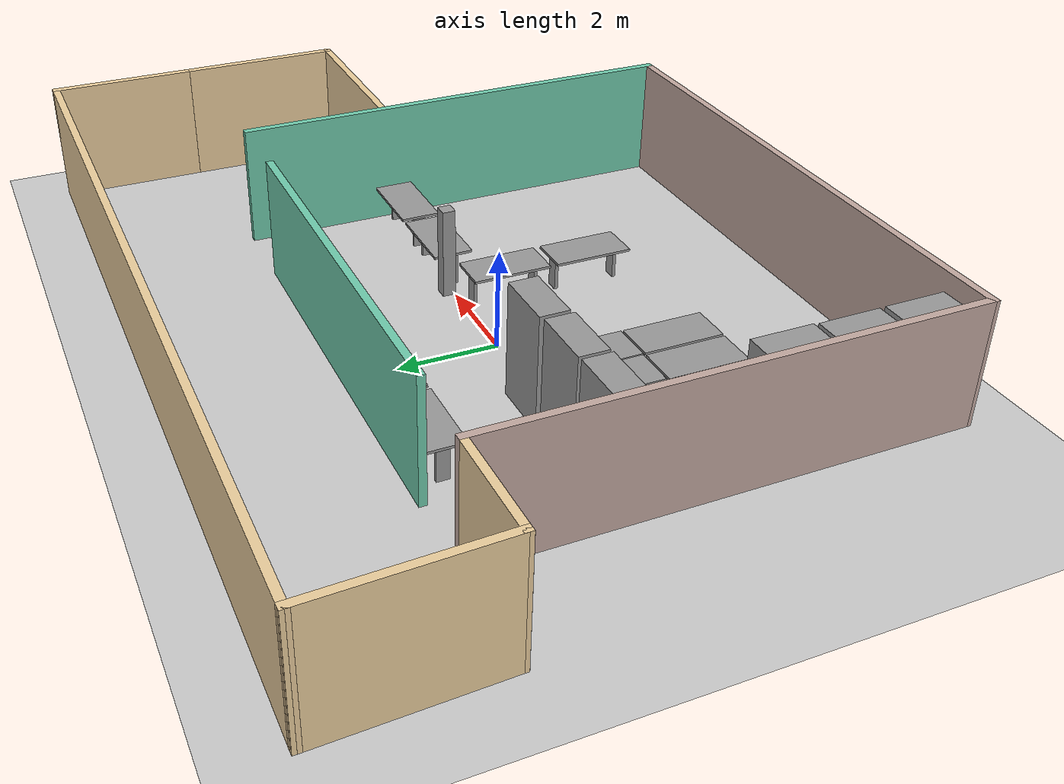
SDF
<sdf version="1.6">
 <world name="default">
  <light name="sun" type="directional">
   <pose>0 0 10 0 -0 0</pose>
   <diffuse>0.8 0.8 0.8 1</diffuse>
   <specular>0.1 0.1 0.1 1</specular>
   <attenuation>
    <range>1000</range>
    <constant>0.9</constant>
    <linear>0.01</linear>
    <quadratic>0.001</quadratic>
   </attenuation>
   <direction>-0.5 0.5 -1</direction>
  </light>
  <model name="ground_plane">
   <static>1</static>
   <link name="link">
    <collision name="collision">
     <geometry><plane><normal>0 0 1</normal><size>100 100</size></plane></geometry>
     <surface><friction><ode><mu>100</mu><mu2>50</mu2></ode></friction></surface>
    </collision>
    <visual name="visual">
     <cast_shadows>0</cast_shadows>
     <geometry><plane><normal>0 0 1</normal><size>100 100</size></plane></geometry>
     <material>
      <script><uri>file://media/materials/scripts/gazebo.material</uri><name>Gazebo/Grey</name></script>
     </material>
    </visual>
   </link>
  </model>
  <gravity>0 0 -9.8</gravity>
  <magnetic_field>6e-06 2.3e-05 -4.2e-05</magnetic_field>
  <atmosphere type="adiabatic"/>
  <physics name="default_physics" default="0" type="ode">
   <max_step_size>0.001</max_step_size>
   <real_time_factor>1</real_time_factor>
   <real_time_update_rate>1000</real_time_update_rate>
  </physics>
  <scene><ambient>0.4 0.4 0.4 1</ambient><background>0.7 0.7 0.7 1</background><shadows>1</shadows></scene>
  <spherical_coordinates>
   <surface_model>EARTH_WGS84</surface_model>
   <latitude_deg>0</latitude_deg>
   <longitude_deg>0</longitude_deg>
   <elevation>0</elevation>
   <heading_deg>0</heading_deg>
  </spherical_coordinates>
  <model name="robot_lab">
   <pose>1.00449 -0.052687 0 0 -0 0</pose>
   <link name="Wall_10">
    <collision name="Wall_10_Collision">
     <geometry><box><size>8 0.15 2.5</size></box></geometry>
     <pose>0 0 1.25 0 -0 0</pose>
    </collision>
    <visual name="Wall_10_Visual">
     <pose>0 0 1.25 0 -0 0</pose>
     <geometry><box><size>8 0.15 2.5</size></box></geometry>
     <material>
      <script><uri>file://media/materials/scripts/gazebo.material</uri><name>Gazebo/Grey</name></script>
      <ambient>0.435294 0.796078 0.67451 1</ambient>
     </material>
    </visual>
    <pose>-0.751583 3.04123 0 0 -0 0</pose>
   </link>
   <link name="Wall_12">
    <collision name="Wall_12_Collision">
     <geometry><box><size>9.5 0.15 2.5</size></box></geometry>
     <pose>0 0 1.25 0 -0 0</pose>
    </collision>
    <visual name="Wall_12_Visual">
     <pose>0 0 1.25 0 -0 0</pose>
     <geometry><box><size>9.5 0.15 2.5</size></box></geometry>
     <material>
      <script><uri>file://media/materials/scripts/gazebo.material</uri><name>Gazebo/Grey</name></script>
      <ambient>0.760784 0.662745 0.627451 1</ambient>
     </material>
    </visual>
    <pose>-6.34573 -1.61098 0 0 0 -1.5708</pose>
   </link>
   <link name="Wall_15">
    <collision name="Wall_15_Collision">
     <geometry><box><size>9.5 0.15 2.5</size></box></geometry>
     <pose>0 0 1.25 0 -0 0</pose>
    </collision>
    <visual name="Wall_15_Visual">
     <pose>0 0 1.25 0 -0 0</pose>
     <geometry><box><size>9.5 0.15 2.5</size></box></geometry>
     <material>
      <script><uri>file://media/materials/scripts/gazebo.material</uri><name>Gazebo/Grey</name></script>
      <ambient>0.435294 0.796078 0.67451 1</ambient>
     </material>
    </visual>
    <pose>4.81922 -1.62974 0 0 0 -1.5708</pose>
   </link>
   <link name="Wall_17">
    <collision name="Wall_17_Collision">
     <geometry><box><size>11.315 0.15 2.5</size></box></geometry>
     <pose>0 0 1.25 0 -0 0</pose>
    </collision>
    <visual name="Wall_17_Visual">
     <pose>0 0 1.25 0 -0 0</pose>
     <geometry><box><size>11.315 0.15 2.5</size></box></geometry>
     <material>
      <script><uri>file://media/materials/scripts/gazebo.material</uri><name>Gazebo/Grey</name></script>
      <ambient>0.760784 0.662745 0.627451 1</ambient>
     </material>
    </visual>
    <pose>-0.763252 -6.29536 0 0 0 -0.00168</pose>
   </link>
   <link name="Wall_25">
    <collision name="Wall_25_Collision">
     <geometry><box><size>17.25 0.15 2.5</size></box></geometry>
     <pose>0 0 1.25 0 -0 0</pose>
    </collision>
    <visual name="Wall_25_Visual">
     <pose>0 0 1.25 0 -0 0</pose>
     <geometry><box><size>17.25 0.15 2.5</size></box></geometry>
     <material>
      <script><uri>file://media/materials/scripts/gazebo.material</uri><name>Gazebo/Grey</name></script>
      <ambient>0.921569 0.807843 0.615686 1</ambient>
     </material>
    </visual>
    <pose>0.001174 6.30252 0 0 -0 0</pose>
   </link>
   <link name="Wall_26">
    <collision name="Wall_26_Collision">
     <geometry><box><size>3 0.15 2.5</size></box></geometry>
     <pose>0 0 1.25 0 -0 0</pose>
    </collision>
    <visual name="Wall_26_Visual">
     <pose>0 0 1.25 0 -0 0</pose>
     <geometry><box><size>3 0.15 2.5</size></box></geometry>
     <material>
      <script><uri>file://media/materials/scripts/gazebo.material</uri><name>Gazebo/Grey</name></script>
      <ambient>0.921569 0.807843 0.615686 1</ambient>
     </material>
    </visual>
    <pose>8.55118 4.87752 0 0 0 -1.5708</pose>
   </link>
   <link name="Wall_28">
    <collision name="Wall_28_Collision">
     <geometry><box><size>2.25 0.15 2.5</size></box></geometry>
     <pose>0 0 1.25 0 -0 0</pose>
    </collision>
    <visual name="Wall_28_Visual">
     <pose>0 0 1.25 0 -0 0</pose>
     <geometry><box><size>2.25 0.15 2.5</size></box></geometry>
     <material>
      <script><uri>file://media/materials/scripts/gazebo.material</uri><name>Gazebo/Grey</name></script>
      <ambient>0.921569 0.807843 0.615686 1</ambient>
     </material>
    </visual>
    <pose>-7.39573 3.06402 0 0 -0 3.14159</pose>
   </link>
   <link name="Wall_32">
    <collision name="Wall_32_Collision">
     <geometry><box><size>3.39014 0.15 2.5</size></box></geometry>
     <pose>0 0 1.25 0 -0 0</pose>
    </collision>
    <visual name="Wall_32_Visual">
     <pose>0 0 1.25 0 -0 0</pose>
     <geometry><box><size>3.39014 0.15 2.5</size></box></geometry>
     <material>
      <script><uri>file://media/materials/scripts/gazebo.material</uri><name>Gazebo/Grey</name></script>
      <ambient>0.921569 0.807843 0.615686 1</ambient>
     </material>
    </visual>
    <pose>-8.49728 4.68327 0 0 0 -1.53897</pose>
   </link>
   <link name="Wall_34">
    <collision name="Wall_34_Collision">
     <geometry><box><size>3.5 0.15 2.5</size></box></geometry>
     <pose>0 0 1.25 0 -0 0</pose>
    </collision>
    <visual name="Wall_34_Visual">
     <pose>0 0 1.25 0 -0 0</pose>
     <geometry><box><size>3.5 0.15 2.5</size></box></geometry>
     <material>
      <script><uri>file://media/materials/scripts/gazebo.material</uri><name>Gazebo/Grey</name></script>
      <ambient>0.921569 0.807843 0.615686 1</ambient>
     </material>
    </visual>
    <pose>8.55118 1.77752 0 0 0 -1.5708</pose>
   </link>
   <link name="Wall_35">
    <collision name="Wall_35_Collision">
     <geometry><box><size>3.75 0.15 2.5</size></box></geometry>
     <pose>0 0 1.25 0 -0 0</pose>
    </collision>
    <visual name="Wall_35_Visual">
     <pose>0 0 1.25 0 -0 0</pose>
     <geometry><box><size>3.75 0.15 2.5</size></box></geometry>
     <material>
      <script><uri>file://media/materials/scripts/gazebo.material</uri><name>Gazebo/Grey</name></script>
      <ambient>0.921569 0.807843 0.615686 1</ambient>
     </material>
    </visual>
    <pose>6.75117 0.10252 0 0 -0 3.14159</pose>
   </link>
   <static>1</static>
  </model>
  <model name="table2_1_2">
   <link name="link_0">
    <pose>0.065308 0.022644 0.260892 0 -0 0</pose>
    <inertial>
     <mass>0.0176486</mass>
     <inertia>
      <ixx>0.00156504</ixx>
      <ixy>0</ixy>
      <ixz>0</ixz>
      <iyy>0.00147786</iyy>
      <iyz>0</iyz>
      <izz>0.00010146</izz>
     </inertia>
    </inertial>
    <visual name="visual">
     <geometry><box><size>0.0697 0.253231 0.7</size></box></geometry>
     <material>
      <lighting>1</lighting>
      <script><uri>file://media/materials/scripts/gazebo.material</uri><name>Gazebo/Grey</name></script>
      <ambient>0.3 0.3 0.3 1</ambient>
      <diffuse>0.7 0.7 0.7 1</diffuse>
      <specular>0.01 0.01 0.01 1</specular>
      <emissive>0 0 0 1</emissive>
      <shader type="vertex"><normal_map>__default__</normal_map></shader>
     </material>
    </visual>
    <collision name="collision">
     <geometry><box><size>0.0697 0.253231 0.7</size></box></geometry>
     <surface>
      <friction>
       <ode><mu>1</mu><mu2>1</mu2><fdir1>0 0 0</fdir1><slip1>0</slip1><slip2>0</slip2></ode>
       <torsional>
        <coefficient>1</coefficient>
        <patch_radius>0</patch_radius>
        <surface_radius>0</surface_radius>
        <use_patch_radius>1</use_patch_radius>
        <ode><slip>0</slip></ode>
       </torsional>
      </friction>
      <bounce><restitution_coefficient>0</restitution_coefficient><threshold>1e+06</threshold></bounce>
      <contact>
       <collide_without_contact>0</collide_without_contact>
       <collide_without_contact_bitmask>1</collide_without_contact_bitmask>
       <collide_bitmask>1</collide_bitmask>
       <ode>
        <soft_cfm>0</soft_cfm>
        <soft_erp>0.2</soft_erp>
        <kp>1e+13</kp>
        <kd>1</kd>
        <max_vel>0.01</max_vel>
        <min_depth>0</min_depth>
       </ode>
       <bullet>
        <split_impulse>1</split_impulse>
        <split_impulse_penetration_threshold>-0.01</split_impulse_penetration_threshold>
        <soft_cfm>0</soft_cfm>
        <soft_erp>0.2</soft_erp>
        <kp>1e+13</kp>
        <kd>1</kd>
       </bullet>
      </contact>
     </surface>
    </collision>
   </link>
   <link name="link_0_clone">
    <pose>1.3547 0.013267 0.260893 0 -0 0</pose>
    <inertial>
     <mass>0.0176486</mass>
     <inertia>
      <ixx>0.00156504</ixx>
      <ixy>0</ixy>
      <ixz>0</ixz>
      <iyy>0.00147786</iyy>
      <iyz>0</iyz>
      <izz>0.00010146</izz>
     </inertia>
    </inertial>
    <visual name="visual">
     <geometry><box><size>0.0697 0.253231 0.7</size></box></geometry>
     <material>
      <lighting>1</lighting>
      <script><uri>file://media/materials/scripts/gazebo.material</uri><name>Gazebo/Grey</name></script>
      <ambient>0.3 0.3 0.3 1</ambient>
      <diffuse>0.7 0.7 0.7 1</diffuse>
      <specular>0.01 0.01 0.01 1</specular>
      <emissive>0 0 0 1</emissive>
      <shader type="vertex"><normal_map>__default__</normal_map></shader>
     </material>
    </visual>
    <collision name="collision">
     <geometry><box><size>0.0697 0.253231 0.7</size></box></geometry>
     <surface>
      <friction>
       <ode><mu>1</mu><mu2>1</mu2><fdir1>0 0 0</fdir1><slip1>0</slip1><slip2>0</slip2></ode>
       <torsional>
        <coefficient>1</coefficient>
        <patch_radius>0</patch_radius>
        <surface_radius>0</surface_radius>
        <use_patch_radius>1</use_patch_radius>
        <ode><slip>0</slip></ode>
       </torsional>
      </friction>
      <bounce><restitution_coefficient>0</restitution_coefficient><threshold>1e+06</threshold></bounce>
      <contact>
       <collide_without_contact>0</collide_without_contact>
       <collide_without_contact_bitmask>1</collide_without_contact_bitmask>
       <collide_bitmask>1</collide_bitmask>
       <ode>
        <soft_cfm>0</soft_cfm>
        <soft_erp>0.2</soft_erp>
        <kp>1e+13</kp>
        <kd>1</kd>
        <max_vel>0.01</max_vel>
        <min_depth>0</min_depth>
       </ode>
       <bullet>
        <split_impulse>1</split_impulse>
        <split_impulse_penetration_threshold>-0.01</split_impulse_penetration_threshold>
        <soft_cfm>0</soft_cfm>
        <soft_erp>0.2</soft_erp>
        <kp>1e+13</kp>
        <kd>1</kd>
       </bullet>
      </contact>
     </surface>
    </collision>
   </link>
   <link name="link_1">
    <pose>0.742636 0.022644 0.617468 0 -0 0</pose>
    <inertial>
     <mass>0.0666298</mass>
     <inertia>
      <ixx>0.00555983</ixx>
      <ixy>0</ixy>
      <ixz>0</ixz>
      <iyy>0.0186674</iyy>
      <iyz>0</iyz>
      <izz>0.0242125</izz>
     </inertia>
    </inertial>
    <visual name="visual">
     <geometry><box><size>1.6 0.8 0.050001</size></box></geometry>
     <material>
      <lighting>1</lighting>
      <script><uri>file://media/materials/scripts/gazebo.material</uri><name>Gazebo/Grey</name></script>
      <ambient>0.3 0.3 0.3 1</ambient>
      <diffuse>0.7 0.7 0.7 1</diffuse>
      <specular>0.01 0.01 0.01 1</specular>
      <emissive>0 0 0 1</emissive>
      <shader type="vertex"><normal_map>__default__</normal_map></shader>
     </material>
    </visual>
    <collision name="collision">
     <geometry><box><size>1.6 0.8 0.050001</size></box></geometry>
     <surface>
      <friction>
       <ode><mu>1000</mu><mu2>1000</mu2><fdir1>0 0 0</fdir1><slip1>0</slip1><slip2>0</slip2></ode>
       <torsional>
        <coefficient>1</coefficient>
        <patch_radius>0</patch_radius>
        <surface_radius>0</surface_radius>
        <use_patch_radius>1</use_patch_radius>
        <ode><slip>0</slip></ode>
       </torsional>
      </friction>
      <bounce><restitution_coefficient>0</restitution_coefficient><threshold>1e+06</threshold></bounce>
      <contact>
       <collide_without_contact>0</collide_without_contact>
       <collide_without_contact_bitmask>1</collide_without_contact_bitmask>
       <collide_bitmask>1</collide_bitmask>
       <ode>
        <soft_cfm>0</soft_cfm>
        <soft_erp>0.2</soft_erp>
        <kp>1e+13</kp>
        <kd>1</kd>
        <max_vel>0.01</max_vel>
        <min_depth>0</min_depth>
       </ode>
       <bullet>
        <split_impulse>1</split_impulse>
        <split_impulse_penetration_threshold>-0.01</split_impulse_penetration_threshold>
        <soft_cfm>0</soft_cfm>
        <soft_erp>0.2</soft_erp>
        <kp>1e+13</kp>
        <kd>1</kd>
       </bullet>
      </contact>
     </surface>
    </collision>
   </link>
   <joint name="link_0_JOINT_0" type="fixed">
    <parent>link_0</parent>
    <child>link_0_clone</child>
    <physics>
     <ode><limit><cfm>0</cfm><erp>0.2</erp></limit><suspension><cfm>0</cfm><erp>0.2</erp></suspension></ode>
    </physics>
   </joint>
   <joint name="link_1_JOINT_1" type="fixed">
    <parent>link_1</parent>
    <child>link_0</child>
    <physics>
     <ode><limit><cfm>0</cfm><erp>0.2</erp></limit><suspension><cfm>0</cfm><erp>0.2</erp></suspension></ode>
    </physics>
   </joint>
   <static>1</static>
   <pose>-3.32099 2.43146 0.099338 0 -0 0</pose>
  </model>
  <model name="table2_1_2_clone">
   <link name="link_0">
    <pose>0.065308 0.022644 0.260892 0 -0 0</pose>
    <inertial>
     <mass>0.0176486</mass>
     <inertia>
      <ixx>0.00156504</ixx>
      <ixy>0</ixy>
      <ixz>0</ixz>
      <iyy>0.00147786</iyy>
      <iyz>0</iyz>
      <izz>0.00010146</izz>
     </inertia>
    </inertial>
    <visual name="visual">
     <geometry><box><size>0.0697 0.253231 0.7</size></box></geometry>
     <material>
      <lighting>1</lighting>
      <script><uri>file://media/materials/scripts/gazebo.material</uri><name>Gazebo/Grey</name></script>
      <ambient>0.3 0.3 0.3 1</ambient>
      <diffuse>0.7 0.7 0.7 1</diffuse>
      <specular>0.01 0.01 0.01 1</specular>
      <emissive>0 0 0 1</emissive>
      <shader type="vertex"><normal_map>__default__</normal_map></shader>
     </material>
    </visual>
    <collision name="collision">
     <geometry><box><size>0.0697 0.253231 0.7</size></box></geometry>
     <surface>
      <friction>
       <ode><mu>1</mu><mu2>1</mu2><fdir1>0 0 0</fdir1><slip1>0</slip1><slip2>0</slip2></ode>
       <torsional>
        <coefficient>1</coefficient>
        <patch_radius>0</patch_radius>
        <surface_radius>0</surface_radius>
        <use_patch_radius>1</use_patch_radius>
        <ode><slip>0</slip></ode>
       </torsional>
      </friction>
      <bounce><restitution_coefficient>0</restitution_coefficient><threshold>1e+06</threshold></bounce>
      <contact>
       <collide_without_contact>0</collide_without_contact>
       <collide_without_contact_bitmask>1</collide_without_contact_bitmask>
       <collide_bitmask>1</collide_bitmask>
       <ode>
        <soft_cfm>0</soft_cfm>
        <soft_erp>0.2</soft_erp>
        <kp>1e+13</kp>
        <kd>1</kd>
        <max_vel>0.01</max_vel>
        <min_depth>0</min_depth>
       </ode>
       <bullet>
        <split_impulse>1</split_impulse>
        <split_impulse_penetration_threshold>-0.01</split_impulse_penetration_threshold>
        <soft_cfm>0</soft_cfm>
        <soft_erp>0.2</soft_erp>
        <kp>1e+13</kp>
        <kd>1</kd>
       </bullet>
      </contact>
     </surface>
    </collision>
   </link>
   <link name="link_0_clone">
    <pose>1.3547 0.013267 0.260893 0 -0 0</pose>
    <inertial>
     <mass>0.0176486</mass>
     <inertia>
      <ixx>0.00156504</ixx>
      <ixy>0</ixy>
      <ixz>0</ixz>
      <iyy>0.00147786</iyy>
      <iyz>0</iyz>
      <izz>0.00010146</izz>
     </inertia>
    </inertial>
    <visual name="visual">
     <geometry><box><size>0.0697 0.253231 0.7</size></box></geometry>
     <material>
      <lighting>1</lighting>
      <script><uri>file://media/materials/scripts/gazebo.material</uri><name>Gazebo/Grey</name></script>
      <ambient>0.3 0.3 0.3 1</ambient>
      <diffuse>0.7 0.7 0.7 1</diffuse>
      <specular>0.01 0.01 0.01 1</specular>
      <emissive>0 0 0 1</emissive>
      <shader type="vertex"><normal_map>__default__</normal_map></shader>
     </material>
    </visual>
    <collision name="collision">
     <geometry><box><size>0.0697 0.253231 0.7</size></box></geometry>
     <surface>
      <friction>
       <ode><mu>1</mu><mu2>1</mu2><fdir1>0 0 0</fdir1><slip1>0</slip1><slip2>0</slip2></ode>
       <torsional>
        <coefficient>1</coefficient>
        <patch_radius>0</patch_radius>
        <surface_radius>0</surface_radius>
        <use_patch_radius>1</use_patch_radius>
        <ode><slip>0</slip></ode>
       </torsional>
      </friction>
      <bounce><restitution_coefficient>0</restitution_coefficient><threshold>1e+06</threshold></bounce>
      <contact>
       <collide_without_contact>0</collide_without_contact>
       <collide_without_contact_bitmask>1</collide_without_contact_bitmask>
       <collide_bitmask>1</collide_bitmask>
       <ode>
        <soft_cfm>0</soft_cfm>
        <soft_erp>0.2</soft_erp>
        <kp>1e+13</kp>
        <kd>1</kd>
        <max_vel>0.01</max_vel>
        <min_depth>0</min_depth>
       </ode>
       <bullet>
        <split_impulse>1</split_impulse>
        <split_impulse_penetration_threshold>-0.01</split_impulse_penetration_threshold>
        <soft_cfm>0</soft_cfm>
        <soft_erp>0.2</soft_erp>
        <kp>1e+13</kp>
        <kd>1</kd>
       </bullet>
      </contact>
     </surface>
    </collision>
   </link>
   <link name="link_1">
    <pose>0.742636 0.022644 0.617468 0 -0 0</pose>
    <inertial>
     <mass>0.0666298</mass>
     <inertia>
      <ixx>0.00555983</ixx>
      <ixy>0</ixy>
      <ixz>0</ixz>
      <iyy>0.0186674</iyy>
      <iyz>0</iyz>
      <izz>0.0242125</izz>
     </inertia>
    </inertial>
    <visual name="visual">
     <geometry><box><size>1.6 0.8 0.050001</size></box></geometry>
     <material>
      <lighting>1</lighting>
      <script><uri>file://media/materials/scripts/gazebo.material</uri><name>Gazebo/Grey</name></script>
      <ambient>0.3 0.3 0.3 1</ambient>
      <diffuse>0.7 0.7 0.7 1</diffuse>
      <specular>0.01 0.01 0.01 1</specular>
      <emissive>0 0 0 1</emissive>
      <shader type="vertex"><normal_map>__default__</normal_map></shader>
     </material>
    </visual>
    <collision name="collision">
     <geometry><box><size>1.6 0.8 0.050001</size></box></geometry>
     <surface>
      <friction>
       <ode><mu>1000</mu><mu2>1000</mu2><fdir1>0 0 0</fdir1><slip1>0</slip1><slip2>0</slip2></ode>
       <torsional>
        <coefficient>1</coefficient>
        <patch_radius>0</patch_radius>
        <surface_radius>0</surface_radius>
        <use_patch_radius>1</use_patch_radius>
        <ode><slip>0</slip></ode>
       </torsional>
      </friction>
      <bounce><restitution_coefficient>0</restitution_coefficient><threshold>1e+06</threshold></bounce>
      <contact>
       <collide_without_contact>0</collide_without_contact>
       <collide_without_contact_bitmask>1</collide_without_contact_bitmask>
       <collide_bitmask>1</collide_bitmask>
       <ode>
        <soft_cfm>0</soft_cfm>
        <soft_erp>0.2</soft_erp>
        <kp>1e+13</kp>
        <kd>1</kd>
        <max_vel>0.01</max_vel>
        <min_depth>0</min_depth>
       </ode>
       <bullet>
        <split_impulse>1</split_impulse>
        <split_impulse_penetration_threshold>-0.01</split_impulse_penetration_threshold>
        <soft_cfm>0</soft_cfm>
        <soft_erp>0.2</soft_erp>
        <kp>1e+13</kp>
        <kd>1</kd>
       </bullet>
      </contact>
     </surface>
    </collision>
   </link>
   <joint name="link_0_JOINT_0" type="fixed">
    <parent>link_0</parent>
    <child>link_0_clone</child>
    <physics>
     <ode><limit><cfm>0</cfm><erp>0.2</erp></limit><suspension><cfm>0</cfm><erp>0.2</erp></suspension></ode>
    </physics>
   </joint>
   <joint name="link_1_JOINT_1" type="fixed">
    <parent>link_1</parent>
    <child>link_0</child>
    <physics>
     <ode><limit><cfm>0</cfm><erp>0.2</erp></limit><suspension><cfm>0</cfm><erp>0.2</erp></suspension></ode>
    </physics>
   </joint>
   <static>1</static>
   <pose>-1.60818 2.44012 0.099338 0 -0 0</pose>
  </model>
  <model name="table2_1_2_clone_0">
   <link name="link_0">
    <pose>0.065308 0.022644 0.260892 0 -0 0</pose>
    <inertial>
     <mass>0.0176486</mass>
     <inertia>
      <ixx>0.00156504</ixx>
      <ixy>0</ixy>
      <ixz>0</ixz>
      <iyy>0.00147786</iyy>
      <iyz>0</iyz>
      <izz>0.00010146</izz>
     </inertia>
    </inertial>
    <visual name="visual">
     <geometry><box><size>0.0697 0.253231 0.7</size></box></geometry>
     <material>
      <lighting>1</lighting>
      <script><uri>file://media/materials/scripts/gazebo.material</uri><name>Gazebo/Grey</name></script>
      <ambient>0.3 0.3 0.3 1</ambient>
      <diffuse>0.7 0.7 0.7 1</diffuse>
      <specular>0.01 0.01 0.01 1</specular>
      <emissive>0 0 0 1</emissive>
      <shader type="vertex"><normal_map>__default__</normal_map></shader>
     </material>
    </visual>
    <collision name="collision">
     <geometry><box><size>0.0697 0.253231 0.7</size></box></geometry>
     <surface>
      <friction>
       <ode><mu>1</mu><mu2>1</mu2><fdir1>0 0 0</fdir1><slip1>0</slip1><slip2>0</slip2></ode>
       <torsional>
        <coefficient>1</coefficient>
        <patch_radius>0</patch_radius>
        <surface_radius>0</surface_radius>
        <use_patch_radius>1</use_patch_radius>
        <ode><slip>0</slip></ode>
       </torsional>
      </friction>
      <bounce><restitution_coefficient>0</restitution_coefficient><threshold>1e+06</threshold></bounce>
      <contact>
       <collide_without_contact>0</collide_without_contact>
       <collide_without_contact_bitmask>1</collide_without_contact_bitmask>
       <collide_bitmask>1</collide_bitmask>
       <ode>
        <soft_cfm>0</soft_cfm>
        <soft_erp>0.2</soft_erp>
        <kp>1e+13</kp>
        <kd>1</kd>
        <max_vel>0.01</max_vel>
        <min_depth>0</min_depth>
       </ode>
       <bullet>
        <split_impulse>1</split_impulse>
        <split_impulse_penetration_threshold>-0.01</split_impulse_penetration_threshold>
        <soft_cfm>0</soft_cfm>
        <soft_erp>0.2</soft_erp>
        <kp>1e+13</kp>
        <kd>1</kd>
       </bullet>
      </contact>
     </surface>
    </collision>
   </link>
   <link name="link_0_clone">
    <pose>1.3547 0.013267 0.260893 0 -0 0</pose>
    <inertial>
     <mass>0.0176486</mass>
     <inertia>
      <ixx>0.00156504</ixx>
      <ixy>0</ixy>
      <ixz>0</ixz>
      <iyy>0.00147786</iyy>
      <iyz>0</iyz>
      <izz>0.00010146</izz>
     </inertia>
    </inertial>
    <visual name="visual">
     <geometry><box><size>0.0697 0.253231 0.7</size></box></geometry>
     <material>
      <lighting>1</lighting>
      <script><uri>file://media/materials/scripts/gazebo.material</uri><name>Gazebo/Grey</name></script>
      <ambient>0.3 0.3 0.3 1</ambient>
      <diffuse>0.7 0.7 0.7 1</diffuse>
      <specular>0.01 0.01 0.01 1</specular>
      <emissive>0 0 0 1</emissive>
      <shader type="vertex"><normal_map>__default__</normal_map></shader>
     </material>
    </visual>
    <collision name="collision">
     <geometry><box><size>0.0697 0.253231 0.7</size></box></geometry>
     <surface>
      <friction>
       <ode><mu>1</mu><mu2>1</mu2><fdir1>0 0 0</fdir1><slip1>0</slip1><slip2>0</slip2></ode>
       <torsional>
        <coefficient>1</coefficient>
        <patch_radius>0</patch_radius>
        <surface_radius>0</surface_radius>
        <use_patch_radius>1</use_patch_radius>
        <ode><slip>0</slip></ode>
       </torsional>
      </friction>
      <bounce><restitution_coefficient>0</restitution_coefficient><threshold>1e+06</threshold></bounce>
      <contact>
       <collide_without_contact>0</collide_without_contact>
       <collide_without_contact_bitmask>1</collide_without_contact_bitmask>
       <collide_bitmask>1</collide_bitmask>
       <ode>
        <soft_cfm>0</soft_cfm>
        <soft_erp>0.2</soft_erp>
        <kp>1e+13</kp>
        <kd>1</kd>
        <max_vel>0.01</max_vel>
        <min_depth>0</min_depth>
       </ode>
       <bullet>
        <split_impulse>1</split_impulse>
        <split_impulse_penetration_threshold>-0.01</split_impulse_penetration_threshold>
        <soft_cfm>0</soft_cfm>
        <soft_erp>0.2</soft_erp>
        <kp>1e+13</kp>
        <kd>1</kd>
       </bullet>
      </contact>
     </surface>
    </collision>
   </link>
   <link name="link_1">
    <pose>0.742636 0.022644 0.617468 0 -0 0</pose>
    <inertial>
     <mass>0.0666298</mass>
     <inertia>
      <ixx>0.00555983</ixx>
      <ixy>0</ixy>
      <ixz>0</ixz>
      <iyy>0.0186674</iyy>
      <iyz>0</iyz>
      <izz>0.0242125</izz>
     </inertia>
    </inertial>
    <visual name="visual">
     <geometry><box><size>1.6 0.8 0.050001</size></box></geometry>
     <material>
      <lighting>1</lighting>
      <script><uri>file://media/materials/scripts/gazebo.material</uri><name>Gazebo/Grey</name></script>
      <ambient>0.3 0.3 0.3 1</ambient>
      <diffuse>0.7 0.7 0.7 1</diffuse>
      <specular>0.01 0.01 0.01 1</specular>
      <emissive>0 0 0 1</emissive>
      <shader type="vertex"><normal_map>__default__</normal_map></shader>
     </material>
    </visual>
    <collision name="collision">
     <geometry><box><size>1.6 0.8 0.050001</size></box></geometry>
     <surface>
      <friction>
       <ode><mu>1000</mu><mu2>1000</mu2><fdir1>0 0 0</fdir1><slip1>0</slip1><slip2>0</slip2></ode>
       <torsional>
        <coefficient>1</coefficient>
        <patch_radius>0</patch_radius>
        <surface_radius>0</surface_radius>
        <use_patch_radius>1</use_patch_radius>
        <ode><slip>0</slip></ode>
       </torsional>
      </friction>
      <bounce><restitution_coefficient>0</restitution_coefficient><threshold>1e+06</threshold></bounce>
      <contact>
       <collide_without_contact>0</collide_without_contact>
       <collide_without_contact_bitmask>1</collide_without_contact_bitmask>
       <collide_bitmask>1</collide_bitmask>
       <ode>
        <soft_cfm>0</soft_cfm>
        <soft_erp>0.2</soft_erp>
        <kp>1e+13</kp>
        <kd>1</kd>
        <max_vel>0.01</max_vel>
        <min_depth>0</min_depth>
       </ode>
       <bullet>
        <split_impulse>1</split_impulse>
        <split_impulse_penetration_threshold>-0.01</split_impulse_penetration_threshold>
        <soft_cfm>0</soft_cfm>
        <soft_erp>0.2</soft_erp>
        <kp>1e+13</kp>
        <kd>1</kd>
       </bullet>
      </contact>
     </surface>
    </collision>
   </link>
   <joint name="link_0_JOINT_0" type="fixed">
    <parent>link_0</parent>
    <child>link_0_clone</child>
    <physics>
     <ode><limit><cfm>0</cfm><erp>0.2</erp></limit><suspension><cfm>0</cfm><erp>0.2</erp></suspension></ode>
    </physics>
   </joint>
   <joint name="link_1_JOINT_1" type="fixed">
    <parent>link_1</parent>
    <child>link_0</child>
    <physics>
     <ode><limit><cfm>0</cfm><erp>0.2</erp></limit><suspension><cfm>0</cfm><erp>0.2</erp></suspension></ode>
    </physics>
   </joint>
   <static>1</static>
   <pose>0.123693 2.41931 0.099338 0 -0 0</pose>
  </model>
  <model name="table2_1_2_clone_0_clone">
   <link name="link_0">
    <pose>0.065308 0.022644 0.260892 0 -0 0</pose>
    <inertial>
     <mass>0.0176486</mass>
     <inertia>
      <ixx>0.00156504</ixx>
      <ixy>0</ixy>
      <ixz>0</ixz>
      <iyy>0.00147786</iyy>
      <iyz>0</iyz>
      <izz>0.00010146</izz>
     </inertia>
    </inertial>
    <visual name="visual">
     <geometry><box><size>0.0697 0.253231 0.7</size></box></geometry>
     <material>
      <lighting>1</lighting>
      <script><uri>file://media/materials/scripts/gazebo.material</uri><name>Gazebo/Grey</name></script>
      <ambient>0.3 0.3 0.3 1</ambient>
      <diffuse>0.7 0.7 0.7 1</diffuse>
      <specular>0.01 0.01 0.01 1</specular>
      <emissive>0 0 0 1</emissive>
      <shader type="vertex"><normal_map>__default__</normal_map></shader>
     </material>
    </visual>
    <collision name="collision">
     <geometry><box><size>0.0697 0.253231 0.7</size></box></geometry>
     <surface>
      <friction>
       <ode><mu>1</mu><mu2>1</mu2><fdir1>0 0 0</fdir1><slip1>0</slip1><slip2>0</slip2></ode>
       <torsional>
        <coefficient>1</coefficient>
        <patch_radius>0</patch_radius>
        <surface_radius>0</surface_radius>
        <use_patch_radius>1</use_patch_radius>
        <ode><slip>0</slip></ode>
       </torsional>
      </friction>
      <bounce><restitution_coefficient>0</restitution_coefficient><threshold>1e+06</threshold></bounce>
      <contact>
       <collide_without_contact>0</collide_without_contact>
       <collide_without_contact_bitmask>1</collide_without_contact_bitmask>
       <collide_bitmask>1</collide_bitmask>
       <ode>
        <soft_cfm>0</soft_cfm>
        <soft_erp>0.2</soft_erp>
        <kp>1e+13</kp>
        <kd>1</kd>
        <max_vel>0.01</max_vel>
        <min_depth>0</min_depth>
       </ode>
       <bullet>
        <split_impulse>1</split_impulse>
        <split_impulse_penetration_threshold>-0.01</split_impulse_penetration_threshold>
        <soft_cfm>0</soft_cfm>
        <soft_erp>0.2</soft_erp>
        <kp>1e+13</kp>
        <kd>1</kd>
       </bullet>
      </contact>
     </surface>
    </collision>
   </link>
   <link name="link_0_clone">
    <pose>1.3547 0.013267 0.260893 0 -0 0</pose>
    <inertial>
     <mass>0.0176486</mass>
     <inertia>
      <ixx>0.00156504</ixx>
      <ixy>0</ixy>
      <ixz>0</ixz>
      <iyy>0.00147786</iyy>
      <iyz>0</iyz>
      <izz>0.00010146</izz>
     </inertia>
    </inertial>
    <visual name="visual">
     <geometry><box><size>0.0697 0.253231 0.7</size></box></geometry>
     <material>
      <lighting>1</lighting>
      <script><uri>file://media/materials/scripts/gazebo.material</uri><name>Gazebo/Grey</name></script>
      <ambient>0.3 0.3 0.3 1</ambient>
      <diffuse>0.7 0.7 0.7 1</diffuse>
      <specular>0.01 0.01 0.01 1</specular>
      <emissive>0 0 0 1</emissive>
      <shader type="vertex"><normal_map>__default__</normal_map></shader>
     </material>
    </visual>
    <collision name="collision">
     <geometry><box><size>0.0697 0.253231 0.7</size></box></geometry>
     <surface>
      <friction>
       <ode><mu>1</mu><mu2>1</mu2><fdir1>0 0 0</fdir1><slip1>0</slip1><slip2>0</slip2></ode>
       <torsional>
        <coefficient>1</coefficient>
        <patch_radius>0</patch_radius>
        <surface_radius>0</surface_radius>
        <use_patch_radius>1</use_patch_radius>
        <ode><slip>0</slip></ode>
       </torsional>
      </friction>
      <bounce><restitution_coefficient>0</restitution_coefficient><threshold>1e+06</threshold></bounce>
      <contact>
       <collide_without_contact>0</collide_without_contact>
       <collide_without_contact_bitmask>1</collide_without_contact_bitmask>
       <collide_bitmask>1</collide_bitmask>
       <ode>
        <soft_cfm>0</soft_cfm>
        <soft_erp>0.2</soft_erp>
        <kp>1e+13</kp>
        <kd>1</kd>
        <max_vel>0.01</max_vel>
        <min_depth>0</min_depth>
       </ode>
       <bullet>
        <split_impulse>1</split_impulse>
        <split_impulse_penetration_threshold>-0.01</split_impulse_penetration_threshold>
        <soft_cfm>0</soft_cfm>
        <soft_erp>0.2</soft_erp>
        <kp>1e+13</kp>
        <kd>1</kd>
       </bullet>
      </contact>
     </surface>
    </collision>
   </link>
   <link name="link_1">
    <pose>0.742636 0.022644 0.617468 0 -0 0</pose>
    <inertial>
     <mass>0.0666298</mass>
     <inertia>
      <ixx>0.00555983</ixx>
      <ixy>0</ixy>
      <ixz>0</ixz>
      <iyy>0.0186674</iyy>
      <iyz>0</iyz>
      <izz>0.0242125</izz>
     </inertia>
    </inertial>
    <visual name="visual">
     <geometry><box><size>1.6 0.8 0.050001</size></box></geometry>
     <material>
      <lighting>1</lighting>
      <script><uri>file://media/materials/scripts/gazebo.material</uri><name>Gazebo/Grey</name></script>
      <ambient>0.3 0.3 0.3 1</ambient>
      <diffuse>0.7 0.7 0.7 1</diffuse>
      <specular>0.01 0.01 0.01 1</specular>
      <emissive>0 0 0 1</emissive>
      <shader type="vertex"><normal_map>__default__</normal_map></shader>
     </material>
    </visual>
    <collision name="collision">
     <geometry><box><size>1.6 0.8 0.050001</size></box></geometry>
     <surface>
      <friction>
       <ode><mu>1000</mu><mu2>1000</mu2><fdir1>0 0 0</fdir1><slip1>0</slip1><slip2>0</slip2></ode>
       <torsional>
        <coefficient>1</coefficient>
        <patch_radius>0</patch_radius>
        <surface_radius>0</surface_radius>
        <use_patch_radius>1</use_patch_radius>
        <ode><slip>0</slip></ode>
       </torsional>
      </friction>
      <bounce><restitution_coefficient>0</restitution_coefficient><threshold>1e+06</threshold></bounce>
      <contact>
       <collide_without_contact>0</collide_without_contact>
       <collide_without_contact_bitmask>1</collide_without_contact_bitmask>
       <collide_bitmask>1</collide_bitmask>
       <ode>
        <soft_cfm>0</soft_cfm>
        <soft_erp>0.2</soft_erp>
        <kp>1e+13</kp>
        <kd>1</kd>
        <max_vel>0.01</max_vel>
        <min_depth>0</min_depth>
       </ode>
       <bullet>
        <split_impulse>1</split_impulse>
        <split_impulse_penetration_threshold>-0.01</split_impulse_penetration_threshold>
        <soft_cfm>0</soft_cfm>
        <soft_erp>0.2</soft_erp>
        <kp>1e+13</kp>
        <kd>1</kd>
       </bullet>
      </contact>
     </surface>
    </collision>
   </link>
   <joint name="link_0_JOINT_0" type="fixed">
    <parent>link_0</parent>
    <child>link_0_clone</child>
    <physics>
     <ode><limit><cfm>0</cfm><erp>0.2</erp></limit><suspension><cfm>0</cfm><erp>0.2</erp></suspension></ode>
    </physics>
   </joint>
   <joint name="link_1_JOINT_1" type="fixed">
    <parent>link_1</parent>
    <child>link_0</child>
    <physics>
     <ode><limit><cfm>0</cfm><erp>0.2</erp></limit><suspension><cfm>0</cfm><erp>0.2</erp></suspension></ode>
    </physics>
   </joint>
   <static>1</static>
   <pose>1.78379 2.41487 0.099338 0 -0 0</pose>
  </model>
  <model name="Closet">
   <link name="link_0">
    <inertial>
     <mass>1.28913</mass>
     <inertia>
      <ixx>0.592801</ixx>
      <ixy>0</ixy>
      <ixz>0</ixz>
      <iyy>0.665886</iyy>
      <iyz>0</iyz>
      <izz>0.14177</izz>
     </inertia>
    </inertial>
    <visual name="visual">
     <geometry><box><size>1.2 0.565387 2.28001</size></box></geometry>
     <material>
      <lighting>1</lighting>
      <script><uri>file://media/materials/scripts/gazebo.material</uri><name>Gazebo/Grey</name></script>
      <ambient>0.3 0.3 0.3 1</ambient>
      <diffuse>0.7 0.7 0.7 1</diffuse>
      <specular>0.01 0.01 0.01 1</specular>
      <emissive>0 0 0 1</emissive>
      <shader type="vertex"><normal_map>__default__</normal_map></shader>
     </material>
    </visual>
    <collision name="collision">
     <geometry><box><size>1.2 0.565387 2.28001</size></box></geometry>
     <surface>
      <friction>
       <ode><mu>1</mu><mu2>1</mu2><fdir1>0 0 0</fdir1><slip1>0</slip1><slip2>0</slip2></ode>
       <torsional>
        <coefficient>1</coefficient>
        <patch_radius>0</patch_radius>
        <surface_radius>0</surface_radius>
        <use_patch_radius>1</use_patch_radius>
        <ode><slip>0</slip></ode>
       </torsional>
      </friction>
      <bounce><restitution_coefficient>0</restitution_coefficient><threshold>1e+06</threshold></bounce>
      <contact>
       <collide_without_contact>0</collide_without_contact>
       <collide_without_contact_bitmask>1</collide_without_contact_bitmask>
       <collide_bitmask>1</collide_bitmask>
       <ode>
        <soft_cfm>0</soft_cfm>
        <soft_erp>0.2</soft_erp>
        <kp>1e+13</kp>
        <kd>1</kd>
        <max_vel>0.01</max_vel>
        <min_depth>0</min_depth>
       </ode>
       <bullet>
        <split_impulse>1</split_impulse>
        <split_impulse_penetration_threshold>-0.01</split_impulse_penetration_threshold>
        <soft_cfm>0</soft_cfm>
        <soft_erp>0.2</soft_erp>
        <kp>1e+13</kp>
        <kd>1</kd>
       </bullet>
      </contact>
     </surface>
    </collision>
   </link>
   <static>0</static>
   <pose>-4.60391 0.162888 1.14001 0 1e-06 0.001911</pose>
  </model>
  <model name="Closet_clone">
   <link name="link_0">
    <inertial>
     <mass>1.28913</mass>
     <inertia>
      <ixx>0.592801</ixx>
      <ixy>0</ixy>
      <ixz>0</ixz>
      <iyy>0.665886</iyy>
      <iyz>0</iyz>
      <izz>0.14177</izz>
     </inertia>
    </inertial>
    <visual name="visual">
     <geometry><box><size>1.2 0.565387 2.28001</size></box></geometry>
     <material>
      <lighting>1</lighting>
      <script><uri>file://media/materials/scripts/gazebo.material</uri><name>Gazebo/Grey</name></script>
      <ambient>0.3 0.3 0.3 1</ambient>
      <diffuse>0.7 0.7 0.7 1</diffuse>
      <specular>0.01 0.01 0.01 1</specular>
      <emissive>0 0 0 1</emissive>
      <shader type="vertex"><normal_map>__default__</normal_map></shader>
     </material>
    </visual>
    <collision name="collision">
     <geometry><box><size>1.2 0.565387 2.28001</size></box></geometry>
     <surface>
      <friction>
       <ode><mu>1</mu><mu2>1</mu2><fdir1>0 0 0</fdir1><slip1>0</slip1><slip2>0</slip2></ode>
       <torsional>
        <coefficient>1</coefficient>
        <patch_radius>0</patch_radius>
        <surface_radius>0</surface_radius>
        <use_patch_radius>1</use_patch_radius>
        <ode><slip>0</slip></ode>
       </torsional>
      </friction>
      <bounce><restitution_coefficient>0</restitution_coefficient><threshold>1e+06</threshold></bounce>
      <contact>
       <collide_without_contact>0</collide_without_contact>
       <collide_without_contact_bitmask>1</collide_without_contact_bitmask>
       <collide_bitmask>1</collide_bitmask>
       <ode>
        <soft_cfm>0</soft_cfm>
        <soft_erp>0.2</soft_erp>
        <kp>1e+13</kp>
        <kd>1</kd>
        <max_vel>0.01</max_vel>
        <min_depth>0</min_depth>
       </ode>
       <bullet>
        <split_impulse>1</split_impulse>
        <split_impulse_penetration_threshold>-0.01</split_impulse_penetration_threshold>
        <soft_cfm>0</soft_cfm>
        <soft_erp>0.2</soft_erp>
        <kp>1e+13</kp>
        <kd>1</kd>
       </bullet>
      </contact>
     </surface>
    </collision>
   </link>
   <static>0</static>
   <pose>-3.33389 0.179448 1.14 1e-06 -2e-06 -0.000639</pose>
  </model>
  <model name="Closet_clone_0">
   <link name="link_0">
    <inertial>
     <mass>1.28913</mass>
     <inertia>
      <ixx>0.592801</ixx>
      <ixy>0</ixy>
      <ixz>0</ixz>
      <iyy>0.665886</iyy>
      <iyz>0</iyz>
      <izz>0.14177</izz>
     </inertia>
    </inertial>
    <visual name="visual">
     <geometry><box><size>1.2 0.565387 2.28001</size></box></geometry>
     <material>
      <lighting>1</lighting>
      <script><uri>file://media/materials/scripts/gazebo.material</uri><name>Gazebo/Grey</name></script>
      <ambient>0.3 0.3 0.3 1</ambient>
      <diffuse>0.7 0.7 0.7 1</diffuse>
      <specular>0.01 0.01 0.01 1</specular>
      <emissive>0 0 0 1</emissive>
      <shader type="vertex"><normal_map>__default__</normal_map></shader>
     </material>
    </visual>
    <collision name="collision">
     <geometry><box><size>1.2 0.565387 2.28001</size></box></geometry>
     <surface>
      <friction>
       <ode><mu>1</mu><mu2>1</mu2><fdir1>0 0 0</fdir1><slip1>0</slip1><slip2>0</slip2></ode>
       <torsional>
        <coefficient>1</coefficient>
        <patch_radius>0</patch_radius>
        <surface_radius>0</surface_radius>
        <use_patch_radius>1</use_patch_radius>
        <ode><slip>0</slip></ode>
       </torsional>
      </friction>
      <bounce><restitution_coefficient>0</restitution_coefficient><threshold>1e+06</threshold></bounce>
      <contact>
       <collide_without_contact>0</collide_without_contact>
       <collide_without_contact_bitmask>1</collide_without_contact_bitmask>
       <collide_bitmask>1</collide_bitmask>
       <ode>
        <soft_cfm>0</soft_cfm>
        <soft_erp>0.2</soft_erp>
        <kp>1e+13</kp>
        <kd>1</kd>
        <max_vel>0.01</max_vel>
        <min_depth>0</min_depth>
       </ode>
       <bullet>
        <split_impulse>1</split_impulse>
        <split_impulse_penetration_threshold>-0.01</split_impulse_penetration_threshold>
        <soft_cfm>0</soft_cfm>
        <soft_erp>0.2</soft_erp>
        <kp>1e+13</kp>
        <kd>1</kd>
       </bullet>
      </contact>
     </surface>
    </collision>
   </link>
   <static>0</static>
   <pose>-2.05089 0.22214 1.14 1e-06 2e-06 0.003028</pose>
  </model>
  <model name="Closet_clone_0_clone">
   <link name="link_0">
    <inertial>
     <mass>1.28913</mass>
     <inertia>
      <ixx>0.592801</ixx>
      <ixy>0</ixy>
      <ixz>0</ixz>
      <iyy>0.665886</iyy>
      <iyz>0</iyz>
      <izz>0.14177</izz>
     </inertia>
    </inertial>
    <visual name="visual">
     <geometry><box><size>1.2 0.565387 2.28001</size></box></geometry>
     <material>
      <lighting>1</lighting>
      <script><uri>file://media/materials/scripts/gazebo.material</uri><name>Gazebo/Grey</name></script>
      <ambient>0.3 0.3 0.3 1</ambient>
      <diffuse>0.7 0.7 0.7 1</diffuse>
      <specular>0.01 0.01 0.01 1</specular>
      <emissive>0 0 0 1</emissive>
      <shader type="vertex"><normal_map>__default__</normal_map></shader>
     </material>
    </visual>
    <collision name="collision">
     <geometry><box><size>1.2 0.565387 2.28001</size></box></geometry>
     <surface>
      <friction>
       <ode><mu>1</mu><mu2>1</mu2><fdir1>0 0 0</fdir1><slip1>0</slip1><slip2>0</slip2></ode>
       <torsional>
        <coefficient>1</coefficient>
        <patch_radius>0</patch_radius>
        <surface_radius>0</surface_radius>
        <use_patch_radius>1</use_patch_radius>
        <ode><slip>0</slip></ode>
       </torsional>
      </friction>
      <bounce><restitution_coefficient>0</restitution_coefficient><threshold>1e+06</threshold></bounce>
      <contact>
       <collide_without_contact>0</collide_without_contact>
       <collide_without_contact_bitmask>1</collide_without_contact_bitmask>
       <collide_bitmask>1</collide_bitmask>
       <ode>
        <soft_cfm>0</soft_cfm>
        <soft_erp>0.2</soft_erp>
        <kp>1e+13</kp>
        <kd>1</kd>
        <max_vel>0.01</max_vel>
        <min_depth>0</min_depth>
       </ode>
       <bullet>
        <split_impulse>1</split_impulse>
        <split_impulse_penetration_threshold>-0.01</split_impulse_penetration_threshold>
        <soft_cfm>0</soft_cfm>
        <soft_erp>0.2</soft_erp>
        <kp>1e+13</kp>
        <kd>1</kd>
       </bullet>
      </contact>
     </surface>
    </collision>
   </link>
   <static>0</static>
   <pose>-4.83721 -5.44636 1.14001 0 1e-06 -1.56738</pose>
  </model>
  <model name="Closet_clone_0_clone_clone">
   <link name="link_0">
    <inertial>
     <mass>1.28913</mass>
     <inertia>
      <ixx>0.592801</ixx>
      <ixy>0</ixy>
      <ixz>0</ixz>
      <iyy>0.665886</iyy>
      <iyz>0</iyz>
      <izz>0.14177</izz>
     </inertia>
    </inertial>
    <visual name="visual">
     <geometry><box><size>1.2 0.565387 2.28001</size></box></geometry>
     <material>
      <lighting>1</lighting>
      <script><uri>file://media/materials/scripts/gazebo.material</uri><name>Gazebo/Grey</name></script>
      <ambient>0.3 0.3 0.3 1</ambient>
      <diffuse>0.7 0.7 0.7 1</diffuse>
      <specular>0.01 0.01 0.01 1</specular>
      <emissive>0 0 0 1</emissive>
      <shader type="vertex"><normal_map>__default__</normal_map></shader>
     </material>
    </visual>
    <collision name="collision">
     <geometry><box><size>1.2 0.565387 2.28001</size></box></geometry>
     <surface>
      <friction>
       <ode><mu>1</mu><mu2>1</mu2><fdir1>0 0 0</fdir1><slip1>0</slip1><slip2>0</slip2></ode>
       <torsional>
        <coefficient>1</coefficient>
        <patch_radius>0</patch_radius>
        <surface_radius>0</surface_radius>
        <use_patch_radius>1</use_patch_radius>
        <ode><slip>0</slip></ode>
       </torsional>
      </friction>
      <bounce><restitution_coefficient>0</restitution_coefficient><threshold>1e+06</threshold></bounce>
      <contact>
       <collide_without_contact>0</collide_without_contact>
       <collide_without_contact_bitmask>1</collide_without_contact_bitmask>
       <collide_bitmask>1</collide_bitmask>
       <ode>
        <soft_cfm>0</soft_cfm>
        <soft_erp>0.2</soft_erp>
        <kp>1e+13</kp>
        <kd>1</kd>
        <max_vel>0.01</max_vel>
        <min_depth>0</min_depth>
       </ode>
       <bullet>
        <split_impulse>1</split_impulse>
        <split_impulse_penetration_threshold>-0.01</split_impulse_penetration_threshold>
        <soft_cfm>0</soft_cfm>
        <soft_erp>0.2</soft_erp>
        <kp>1e+13</kp>
        <kd>1</kd>
       </bullet>
      </contact>
     </surface>
    </collision>
   </link>
   <static>0</static>
   <pose>-4.84303 -4.13441 1.14 -1e-06 2e-06 -1.56672</pose>
  </model>
  <model name="Closet_clone_0_clone_clone_clone">
   <link name="link_0">
    <inertial>
     <mass>1.28913</mass>
     <inertia>
      <ixx>0.592801</ixx>
      <ixy>0</ixy>
      <ixz>0</ixz>
      <iyy>0.665886</iyy>
      <iyz>0</iyz>
      <izz>0.14177</izz>
     </inertia>
    </inertial>
    <visual name="visual">
     <geometry><box><size>1.2 0.565387 2.28001</size></box></geometry>
     <material>
      <lighting>1</lighting>
      <script><uri>file://media/materials/scripts/gazebo.material</uri><name>Gazebo/Grey</name></script>
      <ambient>0.3 0.3 0.3 1</ambient>
      <diffuse>0.7 0.7 0.7 1</diffuse>
      <specular>0.01 0.01 0.01 1</specular>
      <emissive>0 0 0 1</emissive>
      <shader type="vertex"><normal_map>__default__</normal_map></shader>
     </material>
    </visual>
    <collision name="collision">
     <geometry><box><size>1.2 0.565387 2.28001</size></box></geometry>
     <surface>
      <friction>
       <ode><mu>1</mu><mu2>1</mu2><fdir1>0 0 0</fdir1><slip1>0</slip1><slip2>0</slip2></ode>
       <torsional>
        <coefficient>1</coefficient>
        <patch_radius>0</patch_radius>
        <surface_radius>0</surface_radius>
        <use_patch_radius>1</use_patch_radius>
        <ode><slip>0</slip></ode>
       </torsional>
      </friction>
      <bounce><restitution_coefficient>0</restitution_coefficient><threshold>1e+06</threshold></bounce>
      <contact>
       <collide_without_contact>0</collide_without_contact>
       <collide_without_contact_bitmask>1</collide_without_contact_bitmask>
       <collide_bitmask>1</collide_bitmask>
       <ode>
        <soft_cfm>0</soft_cfm>
        <soft_erp>0.2</soft_erp>
        <kp>1e+13</kp>
        <kd>1</kd>
        <max_vel>0.01</max_vel>
        <min_depth>0</min_depth>
       </ode>
       <bullet>
        <split_impulse>1</split_impulse>
        <split_impulse_penetration_threshold>-0.01</split_impulse_penetration_threshold>
        <soft_cfm>0</soft_cfm>
        <soft_erp>0.2</soft_erp>
        <kp>1e+13</kp>
        <kd>1</kd>
       </bullet>
      </contact>
     </surface>
    </collision>
   </link>
   <static>0</static>
   <pose>-4.8171 -2.8545 1.14 1e-06 -2e-06 -1.57671</pose>
  </model>
  <model name="table2_1_2_clone_0_clone_0">
   <link name="link_0">
    <pose>0.065308 0.022644 0.260892 0 -0 0</pose>
    <inertial>
     <mass>0.0176486</mass>
     <inertia>
      <ixx>0.00156504</ixx>
      <ixy>0</ixy>
      <ixz>0</ixz>
      <iyy>0.00147786</iyy>
      <iyz>0</iyz>
      <izz>0.00010146</izz>
     </inertia>
    </inertial>
    <visual name="visual">
     <geometry><box><size>0.0697 0.253231 0.7</size></box></geometry>
     <material>
      <lighting>1</lighting>
      <script><uri>file://media/materials/scripts/gazebo.material</uri><name>Gazebo/Grey</name></script>
      <ambient>0.3 0.3 0.3 1</ambient>
      <diffuse>0.7 0.7 0.7 1</diffuse>
      <specular>0.01 0.01 0.01 1</specular>
      <emissive>0 0 0 1</emissive>
      <shader type="vertex"><normal_map>__default__</normal_map></shader>
     </material>
    </visual>
    <collision name="collision">
     <geometry><box><size>0.0697 0.253231 0.7</size></box></geometry>
     <surface>
      <friction>
       <ode><mu>1</mu><mu2>1</mu2><fdir1>0 0 0</fdir1><slip1>0</slip1><slip2>0</slip2></ode>
       <torsional>
        <coefficient>1</coefficient>
        <patch_radius>0</patch_radius>
        <surface_radius>0</surface_radius>
        <use_patch_radius>1</use_patch_radius>
        <ode><slip>0</slip></ode>
       </torsional>
      </friction>
      <bounce><restitution_coefficient>0</restitution_coefficient><threshold>1e+06</threshold></bounce>
      <contact>
       <collide_without_contact>0</collide_without_contact>
       <collide_without_contact_bitmask>1</collide_without_contact_bitmask>
       <collide_bitmask>1</collide_bitmask>
       <ode>
        <soft_cfm>0</soft_cfm>
        <soft_erp>0.2</soft_erp>
        <kp>1e+13</kp>
        <kd>1</kd>
        <max_vel>0.01</max_vel>
        <min_depth>0</min_depth>
       </ode>
       <bullet>
        <split_impulse>1</split_impulse>
        <split_impulse_penetration_threshold>-0.01</split_impulse_penetration_threshold>
        <soft_cfm>0</soft_cfm>
        <soft_erp>0.2</soft_erp>
        <kp>1e+13</kp>
        <kd>1</kd>
       </bullet>
      </contact>
     </surface>
    </collision>
   </link>
   <link name="link_0_clone">
    <pose>1.3547 0.013267 0.260893 0 -0 0</pose>
    <inertial>
     <mass>0.0176486</mass>
     <inertia>
      <ixx>0.00156504</ixx>
      <ixy>0</ixy>
      <ixz>0</ixz>
      <iyy>0.00147786</iyy>
      <iyz>0</iyz>
      <izz>0.00010146</izz>
     </inertia>
    </inertial>
    <visual name="visual">
     <geometry><box><size>0.0697 0.253231 0.7</size></box></geometry>
     <material>
      <lighting>1</lighting>
      <script><uri>file://media/materials/scripts/gazebo.material</uri><name>Gazebo/Grey</name></script>
      <ambient>0.3 0.3 0.3 1</ambient>
      <diffuse>0.7 0.7 0.7 1</diffuse>
      <specular>0.01 0.01 0.01 1</specular>
      <emissive>0 0 0 1</emissive>
      <shader type="vertex"><normal_map>__default__</normal_map></shader>
     </material>
    </visual>
    <collision name="collision">
     <geometry><box><size>0.0697 0.253231 0.7</size></box></geometry>
     <surface>
      <friction>
       <ode><mu>1</mu><mu2>1</mu2><fdir1>0 0 0</fdir1><slip1>0</slip1><slip2>0</slip2></ode>
       <torsional>
        <coefficient>1</coefficient>
        <patch_radius>0</patch_radius>
        <surface_radius>0</surface_radius>
        <use_patch_radius>1</use_patch_radius>
        <ode><slip>0</slip></ode>
       </torsional>
      </friction>
      <bounce><restitution_coefficient>0</restitution_coefficient><threshold>1e+06</threshold></bounce>
      <contact>
       <collide_without_contact>0</collide_without_contact>
       <collide_without_contact_bitmask>1</collide_without_contact_bitmask>
       <collide_bitmask>1</collide_bitmask>
       <ode>
        <soft_cfm>0</soft_cfm>
        <soft_erp>0.2</soft_erp>
        <kp>1e+13</kp>
        <kd>1</kd>
        <max_vel>0.01</max_vel>
        <min_depth>0</min_depth>
       </ode>
       <bullet>
        <split_impulse>1</split_impulse>
        <split_impulse_penetration_threshold>-0.01</split_impulse_penetration_threshold>
        <soft_cfm>0</soft_cfm>
        <soft_erp>0.2</soft_erp>
        <kp>1e+13</kp>
        <kd>1</kd>
       </bullet>
      </contact>
     </surface>
    </collision>
   </link>
   <link name="link_1">
    <pose>0.742636 0.022644 0.617468 0 -0 0</pose>
    <inertial>
     <mass>0.0666298</mass>
     <inertia>
      <ixx>0.00555983</ixx>
      <ixy>0</ixy>
      <ixz>0</ixz>
      <iyy>0.0186674</iyy>
      <iyz>0</iyz>
      <izz>0.0242125</izz>
     </inertia>
    </inertial>
    <visual name="visual">
     <geometry><box><size>1.6 0.8 0.050001</size></box></geometry>
     <material>
      <lighting>1</lighting>
      <script><uri>file://media/materials/scripts/gazebo.material</uri><name>Gazebo/Grey</name></script>
      <ambient>0.3 0.3 0.3 1</ambient>
      <diffuse>0.7 0.7 0.7 1</diffuse>
      <specular>0.01 0.01 0.01 1</specular>
      <emissive>0 0 0 1</emissive>
      <shader type="vertex"><normal_map>__default__</normal_map></shader>
     </material>
    </visual>
    <collision name="collision">
     <geometry><box><size>1.6 0.8 0.050001</size></box></geometry>
     <surface>
      <friction>
       <ode><mu>1000</mu><mu2>1000</mu2><fdir1>0 0 0</fdir1><slip1>0</slip1><slip2>0</slip2></ode>
       <torsional>
        <coefficient>1</coefficient>
        <patch_radius>0</patch_radius>
        <surface_radius>0</surface_radius>
        <use_patch_radius>1</use_patch_radius>
        <ode><slip>0</slip></ode>
       </torsional>
      </friction>
      <bounce><restitution_coefficient>0</restitution_coefficient><threshold>1e+06</threshold></bounce>
      <contact>
       <collide_without_contact>0</collide_without_contact>
       <collide_without_contact_bitmask>1</collide_without_contact_bitmask>
       <collide_bitmask>1</collide_bitmask>
       <ode>
        <soft_cfm>0</soft_cfm>
        <soft_erp>0.2</soft_erp>
        <kp>1e+13</kp>
        <kd>1</kd>
        <max_vel>0.01</max_vel>
        <min_depth>0</min_depth>
       </ode>
       <bullet>
        <split_impulse>1</split_impulse>
        <split_impulse_penetration_threshold>-0.01</split_impulse_penetration_threshold>
        <soft_cfm>0</soft_cfm>
        <soft_erp>0.2</soft_erp>
        <kp>1e+13</kp>
        <kd>1</kd>
       </bullet>
      </contact>
     </surface>
    </collision>
   </link>
   <joint name="link_0_JOINT_0" type="fixed">
    <parent>link_0</parent>
    <child>link_0_clone</child>
    <physics>
     <ode><limit><cfm>0</cfm><erp>0.2</erp></limit><suspension><cfm>0</cfm><erp>0.2</erp></suspension></ode>
    </physics>
   </joint>
   <joint name="link_1_JOINT_1" type="fixed">
    <parent>link_1</parent>
    <child>link_0</child>
    <physics>
     <ode><limit><cfm>0</cfm><erp>0.2</erp></limit><suspension><cfm>0</cfm><erp>0.2</erp></suspension></ode>
    </physics>
   </joint>
   <static>1</static>
   <pose>4.14636 -0.113667 0.099338 0 -0 0</pose>
  </model>
  <model name="table2_1_2_clone_0_clone_0_clone">
   <link name="link_0">
    <pose>0.065308 0.022644 0.260892 0 -0 0</pose>
    <inertial>
     <mass>0.0176486</mass>
     <inertia>
      <ixx>0.00156504</ixx>
      <ixy>0</ixy>
      <ixz>0</ixz>
      <iyy>0.00147786</iyy>
      <iyz>0</iyz>
      <izz>0.00010146</izz>
     </inertia>
    </inertial>
    <visual name="visual">
     <geometry><box><size>0.0697 0.253231 0.7</size></box></geometry>
     <material>
      <lighting>1</lighting>
      <script><uri>file://media/materials/scripts/gazebo.material</uri><name>Gazebo/Grey</name></script>
      <ambient>0.3 0.3 0.3 1</ambient>
      <diffuse>0.7 0.7 0.7 1</diffuse>
      <specular>0.01 0.01 0.01 1</specular>
      <emissive>0 0 0 1</emissive>
      <shader type="vertex"><normal_map>__default__</normal_map></shader>
     </material>
    </visual>
    <collision name="collision">
     <geometry><box><size>0.0697 0.253231 0.7</size></box></geometry>
     <surface>
      <friction>
       <ode><mu>1</mu><mu2>1</mu2><fdir1>0 0 0</fdir1><slip1>0</slip1><slip2>0</slip2></ode>
       <torsional>
        <coefficient>1</coefficient>
        <patch_radius>0</patch_radius>
        <surface_radius>0</surface_radius>
        <use_patch_radius>1</use_patch_radius>
        <ode><slip>0</slip></ode>
       </torsional>
      </friction>
      <bounce><restitution_coefficient>0</restitution_coefficient><threshold>1e+06</threshold></bounce>
      <contact>
       <collide_without_contact>0</collide_without_contact>
       <collide_without_contact_bitmask>1</collide_without_contact_bitmask>
       <collide_bitmask>1</collide_bitmask>
       <ode>
        <soft_cfm>0</soft_cfm>
        <soft_erp>0.2</soft_erp>
        <kp>1e+13</kp>
        <kd>1</kd>
        <max_vel>0.01</max_vel>
        <min_depth>0</min_depth>
       </ode>
       <bullet>
        <split_impulse>1</split_impulse>
        <split_impulse_penetration_threshold>-0.01</split_impulse_penetration_threshold>
        <soft_cfm>0</soft_cfm>
        <soft_erp>0.2</soft_erp>
        <kp>1e+13</kp>
        <kd>1</kd>
       </bullet>
      </contact>
     </surface>
    </collision>
   </link>
   <link name="link_0_clone">
    <pose>1.3547 0.013267 0.260893 0 -0 0</pose>
    <inertial>
     <mass>0.0176486</mass>
     <inertia>
      <ixx>0.00156504</ixx>
      <ixy>0</ixy>
      <ixz>0</ixz>
      <iyy>0.00147786</iyy>
      <iyz>0</iyz>
      <izz>0.00010146</izz>
     </inertia>
    </inertial>
    <visual name="visual">
     <geometry><box><size>0.0697 0.253231 0.7</size></box></geometry>
     <material>
      <lighting>1</lighting>
      <script><uri>file://media/materials/scripts/gazebo.material</uri><name>Gazebo/Grey</name></script>
      <ambient>0.3 0.3 0.3 1</ambient>
      <diffuse>0.7 0.7 0.7 1</diffuse>
      <specular>0.01 0.01 0.01 1</specular>
      <emissive>0 0 0 1</emissive>
      <shader type="vertex"><normal_map>__default__</normal_map></shader>
     </material>
    </visual>
    <collision name="collision">
     <geometry><box><size>0.0697 0.253231 0.7</size></box></geometry>
     <surface>
      <friction>
       <ode><mu>1</mu><mu2>1</mu2><fdir1>0 0 0</fdir1><slip1>0</slip1><slip2>0</slip2></ode>
       <torsional>
        <coefficient>1</coefficient>
        <patch_radius>0</patch_radius>
        <surface_radius>0</surface_radius>
        <use_patch_radius>1</use_patch_radius>
        <ode><slip>0</slip></ode>
       </torsional>
      </friction>
      <bounce><restitution_coefficient>0</restitution_coefficient><threshold>1e+06</threshold></bounce>
      <contact>
       <collide_without_contact>0</collide_without_contact>
       <collide_without_contact_bitmask>1</collide_without_contact_bitmask>
       <collide_bitmask>1</collide_bitmask>
       <ode>
        <soft_cfm>0</soft_cfm>
        <soft_erp>0.2</soft_erp>
        <kp>1e+13</kp>
        <kd>1</kd>
        <max_vel>0.01</max_vel>
        <min_depth>0</min_depth>
       </ode>
       <bullet>
        <split_impulse>1</split_impulse>
        <split_impulse_penetration_threshold>-0.01</split_impulse_penetration_threshold>
        <soft_cfm>0</soft_cfm>
        <soft_erp>0.2</soft_erp>
        <kp>1e+13</kp>
        <kd>1</kd>
       </bullet>
      </contact>
     </surface>
    </collision>
   </link>
   <link name="link_1">
    <pose>0.742636 0.022644 0.617468 0 -0 0</pose>
    <inertial>
     <mass>0.0666298</mass>
     <inertia>
      <ixx>0.00555983</ixx>
      <ixy>0</ixy>
      <ixz>0</ixz>
      <iyy>0.0186674</iyy>
      <iyz>0</iyz>
      <izz>0.0242125</izz>
     </inertia>
    </inertial>
    <visual name="visual">
     <geometry><box><size>1.6 0.8 0.050001</size></box></geometry>
     <material>
      <lighting>1</lighting>
      <script><uri>file://media/materials/scripts/gazebo.material</uri><name>Gazebo/Grey</name></script>
      <ambient>0.3 0.3 0.3 1</ambient>
      <diffuse>0.7 0.7 0.7 1</diffuse>
      <specular>0.01 0.01 0.01 1</specular>
      <emissive>0 0 0 1</emissive>
      <shader type="vertex"><normal_map>__default__</normal_map></shader>
     </material>
    </visual>
    <collision name="collision">
     <geometry><box><size>1.6 0.8 0.050001</size></box></geometry>
     <surface>
      <friction>
       <ode><mu>1000</mu><mu2>1000</mu2><fdir1>0 0 0</fdir1><slip1>0</slip1><slip2>0</slip2></ode>
       <torsional>
        <coefficient>1</coefficient>
        <patch_radius>0</patch_radius>
        <surface_radius>0</surface_radius>
        <use_patch_radius>1</use_patch_radius>
        <ode><slip>0</slip></ode>
       </torsional>
      </friction>
      <bounce><restitution_coefficient>0</restitution_coefficient><threshold>1e+06</threshold></bounce>
      <contact>
       <collide_without_contact>0</collide_without_contact>
       <collide_without_contact_bitmask>1</collide_without_contact_bitmask>
       <collide_bitmask>1</collide_bitmask>
       <ode>
        <soft_cfm>0</soft_cfm>
        <soft_erp>0.2</soft_erp>
        <kp>1e+13</kp>
        <kd>1</kd>
        <max_vel>0.01</max_vel>
        <min_depth>0</min_depth>
       </ode>
       <bullet>
        <split_impulse>1</split_impulse>
        <split_impulse_penetration_threshold>-0.01</split_impulse_penetration_threshold>
        <soft_cfm>0</soft_cfm>
        <soft_erp>0.2</soft_erp>
        <kp>1e+13</kp>
        <kd>1</kd>
       </bullet>
      </contact>
     </surface>
    </collision>
   </link>
   <joint name="link_0_JOINT_0" type="fixed">
    <parent>link_0</parent>
    <child>link_0_clone</child>
    <physics>
     <ode><limit><cfm>0</cfm><erp>0.2</erp></limit><suspension><cfm>0</cfm><erp>0.2</erp></suspension></ode>
    </physics>
   </joint>
   <joint name="link_1_JOINT_1" type="fixed">
    <parent>link_1</parent>
    <child>link_0</child>
    <physics>
     <ode><limit><cfm>0</cfm><erp>0.2</erp></limit><suspension><cfm>0</cfm><erp>0.2</erp></suspension></ode>
    </physics>
   </joint>
   <static>1</static>
   <pose>2.40738 -0.122017 0.099338 0 -0 0</pose>
  </model>
  <model name="Pole">
   <link name="link">
    <inertial>
     <mass>1</mass>
     <inertia>
      <ixx>0.166667</ixx>
      <ixy>0</ixy>
      <ixz>0</ixz>
      <iyy>0.166667</iyy>
      <iyz>0</iyz>
      <izz>0.166667</izz>
     </inertia>
    </inertial>
    <visual name="visual">
     <geometry><box><size>0.269963 0.25787 1.85987</size></box></geometry>
     <material>
      <script><name>Gazebo/Grey</name><uri>file://media/materials/scripts/gazebo.material</uri></script>
      <ambient>0.3 0.3 0.3 1</ambient>
      <diffuse>0.7 0.7 0.7 1</diffuse>
      <specular>0.01 0.01 0.01 1</specular>
      <emissive>0 0 0 1</emissive>
     </material>
    </visual>
    <collision name="collision">
     <geometry><box><size>0.269963 0.25787 1.85987</size></box></geometry>
     <surface>
      <friction>
       <ode><mu>1</mu><mu2>1</mu2><fdir1>0 0 0</fdir1><slip1>0</slip1><slip2>0</slip2></ode>
       <torsional>
        <coefficient>1</coefficient>
        <patch_radius>0</patch_radius>
        <surface_radius>0</surface_radius>
        <use_patch_radius>1</use_patch_radius>
        <ode><slip>0</slip></ode>
       </torsional>
      </friction>
      <bounce><restitution_coefficient>0</restitution_coefficient><threshold>1e+06</threshold></bounce>
      <contact>
       <collide_without_contact>0</collide_without_contact>
       <collide_without_contact_bitmask>1</collide_without_contact_bitmask>
       <collide_bitmask>1</collide_bitmask>
       <ode>
        <soft_cfm>0</soft_cfm>
        <soft_erp>0.2</soft_erp>
        <kp>1e+13</kp>
        <kd>1</kd>
        <max_vel>0.01</max_vel>
        <min_depth>0</min_depth>
       </ode>
       <bullet>
        <split_impulse>1</split_impulse>
        <split_impulse_penetration_threshold>-0.01</split_impulse_penetration_threshold>
        <soft_cfm>0</soft_cfm>
        <soft_erp>0.2</soft_erp>
        <kp>1e+13</kp>
        <kd>1</kd>
       </bullet>
      </contact>
     </surface>
    </collision>
   </link>
   <static>1</static>
   <pose>2.18471 0.117689 0.929937 -1e-06 -1e-06 0.000115</pose>
  </model>
  <model name="table2_1_2_clone_0_clone_0_clone_0">
   <link name="link_0">
    <pose>0.065308 0.022644 0.260892 0 -0 0</pose>
    <inertial>
     <mass>0.0176486</mass>
     <inertia>
      <ixx>0.00156504</ixx>
      <ixy>0</ixy>
      <ixz>0</ixz>
      <iyy>0.00147786</iyy>
      <iyz>0</iyz>
      <izz>0.00010146</izz>
     </inertia>
    </inertial>
    <visual name="visual">
     <geometry><box><size>0.0697 0.253231 0.7</size></box></geometry>
     <material>
      <lighting>1</lighting>
      <script><uri>file://media/materials/scripts/gazebo.material</uri><name>Gazebo/Grey</name></script>
      <ambient>0.3 0.3 0.3 1</ambient>
      <diffuse>0.7 0.7 0.7 1</diffuse>
      <specular>0.01 0.01 0.01 1</specular>
      <emissive>0 0 0 1</emissive>
      <shader type="vertex"><normal_map>__default__</normal_map></shader>
     </material>
    </visual>
    <collision name="collision">
     <geometry><box><size>0.0697 0.253231 0.7</size></box></geometry>
     <surface>
      <friction>
       <ode><mu>1</mu><mu2>1</mu2><fdir1>0 0 0</fdir1><slip1>0</slip1><slip2>0</slip2></ode>
       <torsional>
        <coefficient>1</coefficient>
        <patch_radius>0</patch_radius>
        <surface_radius>0</surface_radius>
        <use_patch_radius>1</use_patch_radius>
        <ode><slip>0</slip></ode>
       </torsional>
      </friction>
      <bounce><restitution_coefficient>0</restitution_coefficient><threshold>1e+06</threshold></bounce>
      <contact>
       <collide_without_contact>0</collide_without_contact>
       <collide_without_contact_bitmask>1</collide_without_contact_bitmask>
       <collide_bitmask>1</collide_bitmask>
       <ode>
        <soft_cfm>0</soft_cfm>
        <soft_erp>0.2</soft_erp>
        <kp>1e+13</kp>
        <kd>1</kd>
        <max_vel>0.01</max_vel>
        <min_depth>0</min_depth>
       </ode>
       <bullet>
        <split_impulse>1</split_impulse>
        <split_impulse_penetration_threshold>-0.01</split_impulse_penetration_threshold>
        <soft_cfm>0</soft_cfm>
        <soft_erp>0.2</soft_erp>
        <kp>1e+13</kp>
        <kd>1</kd>
       </bullet>
      </contact>
     </surface>
    </collision>
   </link>
   <link name="link_0_clone">
    <pose>1.3547 0.013267 0.260893 0 -0 0</pose>
    <inertial>
     <mass>0.0176486</mass>
     <inertia>
      <ixx>0.00156504</ixx>
      <ixy>0</ixy>
      <ixz>0</ixz>
      <iyy>0.00147786</iyy>
      <iyz>0</iyz>
      <izz>0.00010146</izz>
     </inertia>
    </inertial>
    <visual name="visual">
     <geometry><box><size>0.0697 0.253231 0.7</size></box></geometry>
     <material>
      <lighting>1</lighting>
      <script><uri>file://media/materials/scripts/gazebo.material</uri><name>Gazebo/Grey</name></script>
      <ambient>0.3 0.3 0.3 1</ambient>
      <diffuse>0.7 0.7 0.7 1</diffuse>
      <specular>0.01 0.01 0.01 1</specular>
      <emissive>0 0 0 1</emissive>
      <shader type="vertex"><normal_map>__default__</normal_map></shader>
     </material>
    </visual>
    <collision name="collision">
     <geometry><box><size>0.0697 0.253231 0.7</size></box></geometry>
     <surface>
      <friction>
       <ode><mu>1</mu><mu2>1</mu2><fdir1>0 0 0</fdir1><slip1>0</slip1><slip2>0</slip2></ode>
       <torsional>
        <coefficient>1</coefficient>
        <patch_radius>0</patch_radius>
        <surface_radius>0</surface_radius>
        <use_patch_radius>1</use_patch_radius>
        <ode><slip>0</slip></ode>
       </torsional>
      </friction>
      <bounce><restitution_coefficient>0</restitution_coefficient><threshold>1e+06</threshold></bounce>
      <contact>
       <collide_without_contact>0</collide_without_contact>
       <collide_without_contact_bitmask>1</collide_without_contact_bitmask>
       <collide_bitmask>1</collide_bitmask>
       <ode>
        <soft_cfm>0</soft_cfm>
        <soft_erp>0.2</soft_erp>
        <kp>1e+13</kp>
        <kd>1</kd>
        <max_vel>0.01</max_vel>
        <min_depth>0</min_depth>
       </ode>
       <bullet>
        <split_impulse>1</split_impulse>
        <split_impulse_penetration_threshold>-0.01</split_impulse_penetration_threshold>
        <soft_cfm>0</soft_cfm>
        <soft_erp>0.2</soft_erp>
        <kp>1e+13</kp>
        <kd>1</kd>
       </bullet>
      </contact>
     </surface>
    </collision>
   </link>
   <link name="link_1">
    <pose>0.742636 0.022644 0.617468 0 -0 0</pose>
    <inertial>
     <mass>0.0666298</mass>
     <inertia>
      <ixx>0.00555983</ixx>
      <ixy>0</ixy>
      <ixz>0</ixz>
      <iyy>0.0186674</iyy>
      <iyz>0</iyz>
      <izz>0.0242125</izz>
     </inertia>
    </inertial>
    <visual name="visual">
     <geometry><box><size>1.6 0.8 0.050001</size></box></geometry>
     <material>
      <lighting>1</lighting>
      <script><uri>file://media/materials/scripts/gazebo.material</uri><name>Gazebo/Grey</name></script>
      <ambient>0.3 0.3 0.3 1</ambient>
      <diffuse>0.7 0.7 0.7 1</diffuse>
      <specular>0.01 0.01 0.01 1</specular>
      <emissive>0 0 0 1</emissive>
      <shader type="vertex"><normal_map>__default__</normal_map></shader>
     </material>
    </visual>
    <collision name="collision">
     <geometry><box><size>1.6 0.8 0.050001</size></box></geometry>
     <surface>
      <friction>
       <ode><mu>1000</mu><mu2>1000</mu2><fdir1>0 0 0</fdir1><slip1>0</slip1><slip2>0</slip2></ode>
       <torsional>
        <coefficient>1</coefficient>
        <patch_radius>0</patch_radius>
        <surface_radius>0</surface_radius>
        <use_patch_radius>1</use_patch_radius>
        <ode><slip>0</slip></ode>
       </torsional>
      </friction>
      <bounce><restitution_coefficient>0</restitution_coefficient><threshold>1e+06</threshold></bounce>
      <contact>
       <collide_without_contact>0</collide_without_contact>
       <collide_without_contact_bitmask>1</collide_without_contact_bitmask>
       <collide_bitmask>1</collide_bitmask>
       <ode>
        <soft_cfm>0</soft_cfm>
        <soft_erp>0.2</soft_erp>
        <kp>1e+13</kp>
        <kd>1</kd>
        <max_vel>0.01</max_vel>
        <min_depth>0</min_depth>
       </ode>
       <bullet>
        <split_impulse>1</split_impulse>
        <split_impulse_penetration_threshold>-0.01</split_impulse_penetration_threshold>
        <soft_cfm>0</soft_cfm>
        <soft_erp>0.2</soft_erp>
        <kp>1e+13</kp>
        <kd>1</kd>
       </bullet>
      </contact>
     </surface>
    </collision>
   </link>
   <joint name="link_0_JOINT_0" type="fixed">
    <parent>link_0</parent>
    <child>link_0_clone</child>
    <physics>
     <ode><limit><cfm>0</cfm><erp>0.2</erp></limit><suspension><cfm>0</cfm><erp>0.2</erp></suspension></ode>
    </physics>
   </joint>
   <joint name="link_1_JOINT_1" type="fixed">
    <parent>link_1</parent>
    <child>link_0</child>
    <physics>
     <ode><limit><cfm>0</cfm><erp>0.2</erp></limit><suspension><cfm>0</cfm><erp>0.2</erp></suspension></ode>
    </physics>
   </joint>
   <static>1</static>
   <pose>1.54327 -0.114098 0.099338 0 0 -1.57221</pose>
  </model>
  <model name="table2_1_2_clone_0_clone_0_clone_0_clone">
   <link name="link_0">
    <pose>0.065308 0.022644 0.260892 0 -0 0</pose>
    <inertial>
     <mass>0.0176486</mass>
     <inertia>
      <ixx>0.00156504</ixx>
      <ixy>0</ixy>
      <ixz>0</ixz>
      <iyy>0.00147786</iyy>
      <iyz>0</iyz>
      <izz>0.00010146</izz>
     </inertia>
    </inertial>
    <visual name="visual">
     <geometry><box><size>0.0697 0.253231 0.7</size></box></geometry>
     <material>
      <lighting>1</lighting>
      <script><uri>file://media/materials/scripts/gazebo.material</uri><name>Gazebo/Grey</name></script>
      <ambient>0.3 0.3 0.3 1</ambient>
      <diffuse>0.7 0.7 0.7 1</diffuse>
      <specular>0.01 0.01 0.01 1</specular>
      <emissive>0 0 0 1</emissive>
      <shader type="vertex"><normal_map>__default__</normal_map></shader>
     </material>
    </visual>
    <collision name="collision">
     <geometry><box><size>0.0697 0.253231 0.7</size></box></geometry>
     <surface>
      <friction>
       <ode><mu>1</mu><mu2>1</mu2><fdir1>0 0 0</fdir1><slip1>0</slip1><slip2>0</slip2></ode>
       <torsional>
        <coefficient>1</coefficient>
        <patch_radius>0</patch_radius>
        <surface_radius>0</surface_radius>
        <use_patch_radius>1</use_patch_radius>
        <ode><slip>0</slip></ode>
       </torsional>
      </friction>
      <bounce><restitution_coefficient>0</restitution_coefficient><threshold>1e+06</threshold></bounce>
      <contact>
       <collide_without_contact>0</collide_without_contact>
       <collide_without_contact_bitmask>1</collide_without_contact_bitmask>
       <collide_bitmask>1</collide_bitmask>
       <ode>
        <soft_cfm>0</soft_cfm>
        <soft_erp>0.2</soft_erp>
        <kp>1e+13</kp>
        <kd>1</kd>
        <max_vel>0.01</max_vel>
        <min_depth>0</min_depth>
       </ode>
       <bullet>
        <split_impulse>1</split_impulse>
        <split_impulse_penetration_threshold>-0.01</split_impulse_penetration_threshold>
        <soft_cfm>0</soft_cfm>
        <soft_erp>0.2</soft_erp>
        <kp>1e+13</kp>
        <kd>1</kd>
       </bullet>
      </contact>
     </surface>
    </collision>
   </link>
   <link name="link_0_clone">
    <pose>1.3547 0.013267 0.260893 0 -0 0</pose>
    <inertial>
     <mass>0.0176486</mass>
     <inertia>
      <ixx>0.00156504</ixx>
      <ixy>0</ixy>
      <ixz>0</ixz>
      <iyy>0.00147786</iyy>
      <iyz>0</iyz>
      <izz>0.00010146</izz>
     </inertia>
    </inertial>
    <visual name="visual">
     <geometry><box><size>0.0697 0.253231 0.7</size></box></geometry>
     <material>
      <lighting>1</lighting>
      <script><uri>file://media/materials/scripts/gazebo.material</uri><name>Gazebo/Grey</name></script>
      <ambient>0.3 0.3 0.3 1</ambient>
      <diffuse>0.7 0.7 0.7 1</diffuse>
      <specular>0.01 0.01 0.01 1</specular>
      <emissive>0 0 0 1</emissive>
      <shader type="vertex"><normal_map>__default__</normal_map></shader>
     </material>
    </visual>
    <collision name="collision">
     <geometry><box><size>0.0697 0.253231 0.7</size></box></geometry>
     <surface>
      <friction>
       <ode><mu>1</mu><mu2>1</mu2><fdir1>0 0 0</fdir1><slip1>0</slip1><slip2>0</slip2></ode>
       <torsional>
        <coefficient>1</coefficient>
        <patch_radius>0</patch_radius>
        <surface_radius>0</surface_radius>
        <use_patch_radius>1</use_patch_radius>
        <ode><slip>0</slip></ode>
       </torsional>
      </friction>
      <bounce><restitution_coefficient>0</restitution_coefficient><threshold>1e+06</threshold></bounce>
      <contact>
       <collide_without_contact>0</collide_without_contact>
       <collide_without_contact_bitmask>1</collide_without_contact_bitmask>
       <collide_bitmask>1</collide_bitmask>
       <ode>
        <soft_cfm>0</soft_cfm>
        <soft_erp>0.2</soft_erp>
        <kp>1e+13</kp>
        <kd>1</kd>
        <max_vel>0.01</max_vel>
        <min_depth>0</min_depth>
       </ode>
       <bullet>
        <split_impulse>1</split_impulse>
        <split_impulse_penetration_threshold>-0.01</split_impulse_penetration_threshold>
        <soft_cfm>0</soft_cfm>
        <soft_erp>0.2</soft_erp>
        <kp>1e+13</kp>
        <kd>1</kd>
       </bullet>
      </contact>
     </surface>
    </collision>
   </link>
   <link name="link_1">
    <pose>0.742636 0.022644 0.617468 0 -0 0</pose>
    <inertial>
     <mass>0.0666298</mass>
     <inertia>
      <ixx>0.00555983</ixx>
      <ixy>0</ixy>
      <ixz>0</ixz>
      <iyy>0.0186674</iyy>
      <iyz>0</iyz>
      <izz>0.0242125</izz>
     </inertia>
    </inertial>
    <visual name="visual">
     <geometry><box><size>1.6 0.8 0.050001</size></box></geometry>
     <material>
      <lighting>1</lighting>
      <script><uri>file://media/materials/scripts/gazebo.material</uri><name>Gazebo/Grey</name></script>
      <ambient>0.3 0.3 0.3 1</ambient>
      <diffuse>0.7 0.7 0.7 1</diffuse>
      <specular>0.01 0.01 0.01 1</specular>
      <emissive>0 0 0 1</emissive>
      <shader type="vertex"><normal_map>__default__</normal_map></shader>
     </material>
    </visual>
    <collision name="collision">
     <geometry><box><size>1.6 0.8 0.050001</size></box></geometry>
     <surface>
      <friction>
       <ode><mu>1000</mu><mu2>1000</mu2><fdir1>0 0 0</fdir1><slip1>0</slip1><slip2>0</slip2></ode>
       <torsional>
        <coefficient>1</coefficient>
        <patch_radius>0</patch_radius>
        <surface_radius>0</surface_radius>
        <use_patch_radius>1</use_patch_radius>
        <ode><slip>0</slip></ode>
       </torsional>
      </friction>
      <bounce><restitution_coefficient>0</restitution_coefficient><threshold>1e+06</threshold></bounce>
      <contact>
       <collide_without_contact>0</collide_without_contact>
       <collide_without_contact_bitmask>1</collide_without_contact_bitmask>
       <collide_bitmask>1</collide_bitmask>
       <ode>
        <soft_cfm>0</soft_cfm>
        <soft_erp>0.2</soft_erp>
        <kp>1e+13</kp>
        <kd>1</kd>
        <max_vel>0.01</max_vel>
        <min_depth>0</min_depth>
       </ode>
       <bullet>
        <split_impulse>1</split_impulse>
        <split_impulse_penetration_threshold>-0.01</split_impulse_penetration_threshold>
        <soft_cfm>0</soft_cfm>
        <soft_erp>0.2</soft_erp>
        <kp>1e+13</kp>
        <kd>1</kd>
       </bullet>
      </contact>
     </surface>
    </collision>
   </link>
   <joint name="link_0_JOINT_0" type="fixed">
    <parent>link_0</parent>
    <child>link_0_clone</child>
    <physics>
     <ode><limit><cfm>0</cfm><erp>0.2</erp></limit><suspension><cfm>0</cfm><erp>0.2</erp></suspension></ode>
    </physics>
   </joint>
   <joint name="link_1_JOINT_1" type="fixed">
    <parent>link_1</parent>
    <child>link_0</child>
    <physics>
     <ode><limit><cfm>0</cfm><erp>0.2</erp></limit><suspension><cfm>0</cfm><erp>0.2</erp></suspension></ode>
    </physics>
   </joint>
   <static>1</static>
   <pose>1.54005 -1.86723 0.099338 0 0 -1.57221</pose>
  </model>
  <model name="table2_1_2_clone_0_clone_0_clone_0_clone_0">
   <link name="link_0">
    <pose>0.065308 0.022644 0.260892 0 -0 0</pose>
    <inertial>
     <mass>0.0176486</mass>
     <inertia>
      <ixx>0.00156504</ixx>
      <ixy>0</ixy>
      <ixz>0</ixz>
      <iyy>0.00147786</iyy>
      <iyz>0</iyz>
      <izz>0.00010146</izz>
     </inertia>
    </inertial>
    <visual name="visual">
     <geometry><box><size>0.0697 0.253231 0.7</size></box></geometry>
     <material>
      <lighting>1</lighting>
      <script><uri>file://media/materials/scripts/gazebo.material</uri><name>Gazebo/Grey</name></script>
      <ambient>0.3 0.3 0.3 1</ambient>
      <diffuse>0.7 0.7 0.7 1</diffuse>
      <specular>0.01 0.01 0.01 1</specular>
      <emissive>0 0 0 1</emissive>
      <shader type="vertex"><normal_map>__default__</normal_map></shader>
     </material>
    </visual>
    <collision name="collision">
     <geometry><box><size>0.0697 0.253231 0.7</size></box></geometry>
     <surface>
      <friction>
       <ode><mu>1</mu><mu2>1</mu2><fdir1>0 0 0</fdir1><slip1>0</slip1><slip2>0</slip2></ode>
       <torsional>
        <coefficient>1</coefficient>
        <patch_radius>0</patch_radius>
        <surface_radius>0</surface_radius>
        <use_patch_radius>1</use_patch_radius>
        <ode><slip>0</slip></ode>
       </torsional>
      </friction>
      <bounce><restitution_coefficient>0</restitution_coefficient><threshold>1e+06</threshold></bounce>
      <contact>
       <collide_without_contact>0</collide_without_contact>
       <collide_without_contact_bitmask>1</collide_without_contact_bitmask>
       <collide_bitmask>1</collide_bitmask>
       <ode>
        <soft_cfm>0</soft_cfm>
        <soft_erp>0.2</soft_erp>
        <kp>1e+13</kp>
        <kd>1</kd>
        <max_vel>0.01</max_vel>
        <min_depth>0</min_depth>
       </ode>
       <bullet>
        <split_impulse>1</split_impulse>
        <split_impulse_penetration_threshold>-0.01</split_impulse_penetration_threshold>
        <soft_cfm>0</soft_cfm>
        <soft_erp>0.2</soft_erp>
        <kp>1e+13</kp>
        <kd>1</kd>
       </bullet>
      </contact>
     </surface>
    </collision>
   </link>
   <link name="link_0_clone">
    <pose>1.3547 0.013267 0.260893 0 -0 0</pose>
    <inertial>
     <mass>0.0176486</mass>
     <inertia>
      <ixx>0.00156504</ixx>
      <ixy>0</ixy>
      <ixz>0</ixz>
      <iyy>0.00147786</iyy>
      <iyz>0</iyz>
      <izz>0.00010146</izz>
     </inertia>
    </inertial>
    <visual name="visual">
     <geometry><box><size>0.0697 0.253231 0.7</size></box></geometry>
     <material>
      <lighting>1</lighting>
      <script><uri>file://media/materials/scripts/gazebo.material</uri><name>Gazebo/Grey</name></script>
      <ambient>0.3 0.3 0.3 1</ambient>
      <diffuse>0.7 0.7 0.7 1</diffuse>
      <specular>0.01 0.01 0.01 1</specular>
      <emissive>0 0 0 1</emissive>
      <shader type="vertex"><normal_map>__default__</normal_map></shader>
     </material>
    </visual>
    <collision name="collision">
     <geometry><box><size>0.0697 0.253231 0.7</size></box></geometry>
     <surface>
      <friction>
       <ode><mu>1</mu><mu2>1</mu2><fdir1>0 0 0</fdir1><slip1>0</slip1><slip2>0</slip2></ode>
       <torsional>
        <coefficient>1</coefficient>
        <patch_radius>0</patch_radius>
        <surface_radius>0</surface_radius>
        <use_patch_radius>1</use_patch_radius>
        <ode><slip>0</slip></ode>
       </torsional>
      </friction>
      <bounce><restitution_coefficient>0</restitution_coefficient><threshold>1e+06</threshold></bounce>
      <contact>
       <collide_without_contact>0</collide_without_contact>
       <collide_without_contact_bitmask>1</collide_without_contact_bitmask>
       <collide_bitmask>1</collide_bitmask>
       <ode>
        <soft_cfm>0</soft_cfm>
        <soft_erp>0.2</soft_erp>
        <kp>1e+13</kp>
        <kd>1</kd>
        <max_vel>0.01</max_vel>
        <min_depth>0</min_depth>
       </ode>
       <bullet>
        <split_impulse>1</split_impulse>
        <split_impulse_penetration_threshold>-0.01</split_impulse_penetration_threshold>
        <soft_cfm>0</soft_cfm>
        <soft_erp>0.2</soft_erp>
        <kp>1e+13</kp>
        <kd>1</kd>
       </bullet>
      </contact>
     </surface>
    </collision>
   </link>
   <link name="link_1">
    <pose>0.742636 0.022644 0.617468 0 -0 0</pose>
    <inertial>
     <mass>0.0666298</mass>
     <inertia>
      <ixx>0.00555983</ixx>
      <ixy>0</ixy>
      <ixz>0</ixz>
      <iyy>0.0186674</iyy>
      <iyz>0</iyz>
      <izz>0.0242125</izz>
     </inertia>
    </inertial>
    <visual name="visual">
     <geometry><box><size>1.6 0.8 0.050001</size></box></geometry>
     <material>
      <lighting>1</lighting>
      <script><uri>file://media/materials/scripts/gazebo.material</uri><name>Gazebo/Grey</name></script>
      <ambient>0.3 0.3 0.3 1</ambient>
      <diffuse>0.7 0.7 0.7 1</diffuse>
      <specular>0.01 0.01 0.01 1</specular>
      <emissive>0 0 0 1</emissive>
      <shader type="vertex"><normal_map>__default__</normal_map></shader>
     </material>
    </visual>
    <collision name="collision">
     <geometry><box><size>1.6 0.8 0.050001</size></box></geometry>
     <surface>
      <friction>
       <ode><mu>1000</mu><mu2>1000</mu2><fdir1>0 0 0</fdir1><slip1>0</slip1><slip2>0</slip2></ode>
       <torsional>
        <coefficient>1</coefficient>
        <patch_radius>0</patch_radius>
        <surface_radius>0</surface_radius>
        <use_patch_radius>1</use_patch_radius>
        <ode><slip>0</slip></ode>
       </torsional>
      </friction>
      <bounce><restitution_coefficient>0</restitution_coefficient><threshold>1e+06</threshold></bounce>
      <contact>
       <collide_without_contact>0</collide_without_contact>
       <collide_without_contact_bitmask>1</collide_without_contact_bitmask>
       <collide_bitmask>1</collide_bitmask>
       <ode>
        <soft_cfm>0</soft_cfm>
        <soft_erp>0.2</soft_erp>
        <kp>1e+13</kp>
        <kd>1</kd>
        <max_vel>0.01</max_vel>
        <min_depth>0</min_depth>
       </ode>
       <bullet>
        <split_impulse>1</split_impulse>
        <split_impulse_penetration_threshold>-0.01</split_impulse_penetration_threshold>
        <soft_cfm>0</soft_cfm>
        <soft_erp>0.2</soft_erp>
        <kp>1e+13</kp>
        <kd>1</kd>
       </bullet>
      </contact>
     </surface>
    </collision>
   </link>
   <joint name="link_0_JOINT_0" type="fixed">
    <parent>link_0</parent>
    <child>link_0_clone</child>
    <physics>
     <ode><limit><cfm>0</cfm><erp>0.2</erp></limit><suspension><cfm>0</cfm><erp>0.2</erp></suspension></ode>
    </physics>
   </joint>
   <joint name="link_1_JOINT_1" type="fixed">
    <parent>link_1</parent>
    <child>link_0</child>
    <physics>
     <ode><limit><cfm>0</cfm><erp>0.2</erp></limit><suspension><cfm>0</cfm><erp>0.2</erp></suspension></ode>
    </physics>
   </joint>
   <static>1</static>
   <pose>-1.86025 -0.230832 0.099338 0 0 -1.57221</pose>
  </model>
  <model name="table2_1_2_clone_0_clone_0_clone_0_clone_1">
   <link name="link_0">
    <pose>0.065308 0.022644 0.260892 0 -0 0</pose>
    <inertial>
     <mass>0.0176486</mass>
     <inertia>
      <ixx>0.00156504</ixx>
      <ixy>0</ixy>
      <ixz>0</ixz>
      <iyy>0.00147786</iyy>
      <iyz>0</iyz>
      <izz>0.00010146</izz>
     </inertia>
    </inertial>
    <visual name="visual">
     <geometry><box><size>0.0697 0.253231 0.7</size></box></geometry>
     <material>
      <lighting>1</lighting>
      <script><uri>file://media/materials/scripts/gazebo.material</uri><name>Gazebo/Grey</name></script>
      <ambient>0.3 0.3 0.3 1</ambient>
      <diffuse>0.7 0.7 0.7 1</diffuse>
      <specular>0.01 0.01 0.01 1</specular>
      <emissive>0 0 0 1</emissive>
      <shader type="vertex"><normal_map>__default__</normal_map></shader>
     </material>
    </visual>
    <collision name="collision">
     <geometry><box><size>0.0697 0.253231 0.7</size></box></geometry>
     <surface>
      <friction>
       <ode><mu>1</mu><mu2>1</mu2><fdir1>0 0 0</fdir1><slip1>0</slip1><slip2>0</slip2></ode>
       <torsional>
        <coefficient>1</coefficient>
        <patch_radius>0</patch_radius>
        <surface_radius>0</surface_radius>
        <use_patch_radius>1</use_patch_radius>
        <ode><slip>0</slip></ode>
       </torsional>
      </friction>
      <bounce><restitution_coefficient>0</restitution_coefficient><threshold>1e+06</threshold></bounce>
      <contact>
       <collide_without_contact>0</collide_without_contact>
       <collide_without_contact_bitmask>1</collide_without_contact_bitmask>
       <collide_bitmask>1</collide_bitmask>
       <ode>
        <soft_cfm>0</soft_cfm>
        <soft_erp>0.2</soft_erp>
        <kp>1e+13</kp>
        <kd>1</kd>
        <max_vel>0.01</max_vel>
        <min_depth>0</min_depth>
       </ode>
       <bullet>
        <split_impulse>1</split_impulse>
        <split_impulse_penetration_threshold>-0.01</split_impulse_penetration_threshold>
        <soft_cfm>0</soft_cfm>
        <soft_erp>0.2</soft_erp>
        <kp>1e+13</kp>
        <kd>1</kd>
       </bullet>
      </contact>
     </surface>
    </collision>
   </link>
   <link name="link_0_clone">
    <pose>1.3547 0.013267 0.260893 0 -0 0</pose>
    <inertial>
     <mass>0.0176486</mass>
     <inertia>
      <ixx>0.00156504</ixx>
      <ixy>0</ixy>
      <ixz>0</ixz>
      <iyy>0.00147786</iyy>
      <iyz>0</iyz>
      <izz>0.00010146</izz>
     </inertia>
    </inertial>
    <visual name="visual">
     <geometry><box><size>0.0697 0.253231 0.7</size></box></geometry>
     <material>
      <lighting>1</lighting>
      <script><uri>file://media/materials/scripts/gazebo.material</uri><name>Gazebo/Grey</name></script>
      <ambient>0.3 0.3 0.3 1</ambient>
      <diffuse>0.7 0.7 0.7 1</diffuse>
      <specular>0.01 0.01 0.01 1</specular>
      <emissive>0 0 0 1</emissive>
      <shader type="vertex"><normal_map>__default__</normal_map></shader>
     </material>
    </visual>
    <collision name="collision">
     <geometry><box><size>0.0697 0.253231 0.7</size></box></geometry>
     <surface>
      <friction>
       <ode><mu>1</mu><mu2>1</mu2><fdir1>0 0 0</fdir1><slip1>0</slip1><slip2>0</slip2></ode>
       <torsional>
        <coefficient>1</coefficient>
        <patch_radius>0</patch_radius>
        <surface_radius>0</surface_radius>
        <use_patch_radius>1</use_patch_radius>
        <ode><slip>0</slip></ode>
       </torsional>
      </friction>
      <bounce><restitution_coefficient>0</restitution_coefficient><threshold>1e+06</threshold></bounce>
      <contact>
       <collide_without_contact>0</collide_without_contact>
       <collide_without_contact_bitmask>1</collide_without_contact_bitmask>
       <collide_bitmask>1</collide_bitmask>
       <ode>
        <soft_cfm>0</soft_cfm>
        <soft_erp>0.2</soft_erp>
        <kp>1e+13</kp>
        <kd>1</kd>
        <max_vel>0.01</max_vel>
        <min_depth>0</min_depth>
       </ode>
       <bullet>
        <split_impulse>1</split_impulse>
        <split_impulse_penetration_threshold>-0.01</split_impulse_penetration_threshold>
        <soft_cfm>0</soft_cfm>
        <soft_erp>0.2</soft_erp>
        <kp>1e+13</kp>
        <kd>1</kd>
       </bullet>
      </contact>
     </surface>
    </collision>
   </link>
   <link name="link_1">
    <pose>0.742636 0.022644 0.617468 0 -0 0</pose>
    <inertial>
     <mass>0.0666298</mass>
     <inertia>
      <ixx>0.00555983</ixx>
      <ixy>0</ixy>
      <ixz>0</ixz>
      <iyy>0.0186674</iyy>
      <iyz>0</iyz>
      <izz>0.0242125</izz>
     </inertia>
    </inertial>
    <visual name="visual">
     <geometry><box><size>1.6 0.8 0.050001</size></box></geometry>
     <material>
      <lighting>1</lighting>
      <script><uri>file://media/materials/scripts/gazebo.material</uri><name>Gazebo/Grey</name></script>
      <ambient>0.3 0.3 0.3 1</ambient>
      <diffuse>0.7 0.7 0.7 1</diffuse>
      <specular>0.01 0.01 0.01 1</specular>
      <emissive>0 0 0 1</emissive>
      <shader type="vertex"><normal_map>__default__</normal_map></shader>
     </material>
    </visual>
    <collision name="collision">
     <geometry><box><size>1.6 0.8 0.050001</size></box></geometry>
     <surface>
      <friction>
       <ode><mu>1000</mu><mu2>1000</mu2><fdir1>0 0 0</fdir1><slip1>0</slip1><slip2>0</slip2></ode>
       <torsional>
        <coefficient>1</coefficient>
        <patch_radius>0</patch_radius>
        <surface_radius>0</surface_radius>
        <use_patch_radius>1</use_patch_radius>
        <ode><slip>0</slip></ode>
       </torsional>
      </friction>
      <bounce><restitution_coefficient>0</restitution_coefficient><threshold>1e+06</threshold></bounce>
      <contact>
       <collide_without_contact>0</collide_without_contact>
       <collide_without_contact_bitmask>1</collide_without_contact_bitmask>
       <collide_bitmask>1</collide_bitmask>
       <ode>
        <soft_cfm>0</soft_cfm>
        <soft_erp>0.2</soft_erp>
        <kp>1e+13</kp>
        <kd>1</kd>
        <max_vel>0.01</max_vel>
        <min_depth>0</min_depth>
       </ode>
       <bullet>
        <split_impulse>1</split_impulse>
        <split_impulse_penetration_threshold>-0.01</split_impulse_penetration_threshold>
        <soft_cfm>0</soft_cfm>
        <soft_erp>0.2</soft_erp>
        <kp>1e+13</kp>
        <kd>1</kd>
       </bullet>
      </contact>
     </surface>
    </collision>
   </link>
   <joint name="link_0_JOINT_0" type="fixed">
    <parent>link_0</parent>
    <child>link_0_clone</child>
    <physics>
     <ode><limit><cfm>0</cfm><erp>0.2</erp></limit><suspension><cfm>0</cfm><erp>0.2</erp></suspension></ode>
    </physics>
   </joint>
   <joint name="link_1_JOINT_1" type="fixed">
    <parent>link_1</parent>
    <child>link_0</child>
    <physics>
     <ode><limit><cfm>0</cfm><erp>0.2</erp></limit><suspension><cfm>0</cfm><erp>0.2</erp></suspension></ode>
    </physics>
   </joint>
   <static>1</static>
   <pose>-2.69141 -0.209288 0.099338 0 0 -1.57221</pose>
  </model>
  <model name="table2_1_2_clone_0_clone_0_clone_0_clone_0_clone">
   <link name="link_0">
    <pose>0.065308 0.022644 0.260892 0 -0 0</pose>
    <inertial>
     <mass>0.0176486</mass>
     <inertia>
      <ixx>0.00156504</ixx>
      <ixy>0</ixy>
      <ixz>0</ixz>
      <iyy>0.00147786</iyy>
      <iyz>0</iyz>
      <izz>0.00010146</izz>
     </inertia>
    </inertial>
    <visual name="visual">
     <geometry><box><size>0.0697 0.253231 0.7</size></box></geometry>
     <material>
      <lighting>1</lighting>
      <script><uri>file://media/materials/scripts/gazebo.material</uri><name>Gazebo/Grey</name></script>
      <ambient>0.3 0.3 0.3 1</ambient>
      <diffuse>0.7 0.7 0.7 1</diffuse>
      <specular>0.01 0.01 0.01 1</specular>
      <emissive>0 0 0 1</emissive>
      <shader type="vertex"><normal_map>__default__</normal_map></shader>
     </material>
    </visual>
    <collision name="collision">
     <geometry><box><size>0.0697 0.253231 0.7</size></box></geometry>
     <surface>
      <friction>
       <ode><mu>1</mu><mu2>1</mu2><fdir1>0 0 0</fdir1><slip1>0</slip1><slip2>0</slip2></ode>
       <torsional>
        <coefficient>1</coefficient>
        <patch_radius>0</patch_radius>
        <surface_radius>0</surface_radius>
        <use_patch_radius>1</use_patch_radius>
        <ode><slip>0</slip></ode>
       </torsional>
      </friction>
      <bounce><restitution_coefficient>0</restitution_coefficient><threshold>1e+06</threshold></bounce>
      <contact>
       <collide_without_contact>0</collide_without_contact>
       <collide_without_contact_bitmask>1</collide_without_contact_bitmask>
       <collide_bitmask>1</collide_bitmask>
       <ode>
        <soft_cfm>0</soft_cfm>
        <soft_erp>0.2</soft_erp>
        <kp>1e+13</kp>
        <kd>1</kd>
        <max_vel>0.01</max_vel>
        <min_depth>0</min_depth>
       </ode>
       <bullet>
        <split_impulse>1</split_impulse>
        <split_impulse_penetration_threshold>-0.01</split_impulse_penetration_threshold>
        <soft_cfm>0</soft_cfm>
        <soft_erp>0.2</soft_erp>
        <kp>1e+13</kp>
        <kd>1</kd>
       </bullet>
      </contact>
     </surface>
    </collision>
   </link>
   <link name="link_0_clone">
    <pose>1.3547 0.013267 0.260893 0 -0 0</pose>
    <inertial>
     <mass>0.0176486</mass>
     <inertia>
      <ixx>0.00156504</ixx>
      <ixy>0</ixy>
      <ixz>0</ixz>
      <iyy>0.00147786</iyy>
      <iyz>0</iyz>
      <izz>0.00010146</izz>
     </inertia>
    </inertial>
    <visual name="visual">
     <geometry><box><size>0.0697 0.253231 0.7</size></box></geometry>
     <material>
      <lighting>1</lighting>
      <script><uri>file://media/materials/scripts/gazebo.material</uri><name>Gazebo/Grey</name></script>
      <ambient>0.3 0.3 0.3 1</ambient>
      <diffuse>0.7 0.7 0.7 1</diffuse>
      <specular>0.01 0.01 0.01 1</specular>
      <emissive>0 0 0 1</emissive>
      <shader type="vertex"><normal_map>__default__</normal_map></shader>
     </material>
    </visual>
    <collision name="collision">
     <geometry><box><size>0.0697 0.253231 0.7</size></box></geometry>
     <surface>
      <friction>
       <ode><mu>1</mu><mu2>1</mu2><fdir1>0 0 0</fdir1><slip1>0</slip1><slip2>0</slip2></ode>
       <torsional>
        <coefficient>1</coefficient>
        <patch_radius>0</patch_radius>
        <surface_radius>0</surface_radius>
        <use_patch_radius>1</use_patch_radius>
        <ode><slip>0</slip></ode>
       </torsional>
      </friction>
      <bounce><restitution_coefficient>0</restitution_coefficient><threshold>1e+06</threshold></bounce>
      <contact>
       <collide_without_contact>0</collide_without_contact>
       <collide_without_contact_bitmask>1</collide_without_contact_bitmask>
       <collide_bitmask>1</collide_bitmask>
       <ode>
        <soft_cfm>0</soft_cfm>
        <soft_erp>0.2</soft_erp>
        <kp>1e+13</kp>
        <kd>1</kd>
        <max_vel>0.01</max_vel>
        <min_depth>0</min_depth>
       </ode>
       <bullet>
        <split_impulse>1</split_impulse>
        <split_impulse_penetration_threshold>-0.01</split_impulse_penetration_threshold>
        <soft_cfm>0</soft_cfm>
        <soft_erp>0.2</soft_erp>
        <kp>1e+13</kp>
        <kd>1</kd>
       </bullet>
      </contact>
     </surface>
    </collision>
   </link>
   <link name="link_1">
    <pose>0.742636 0.022644 0.617468 0 -0 0</pose>
    <inertial>
     <mass>0.0666298</mass>
     <inertia>
      <ixx>0.00555983</ixx>
      <ixy>0</ixy>
      <ixz>0</ixz>
      <iyy>0.0186674</iyy>
      <iyz>0</iyz>
      <izz>0.0242125</izz>
     </inertia>
    </inertial>
    <visual name="visual">
     <geometry><box><size>1.6 0.8 0.050001</size></box></geometry>
     <material>
      <lighting>1</lighting>
      <script><uri>file://media/materials/scripts/gazebo.material</uri><name>Gazebo/Grey</name></script>
      <ambient>0.3 0.3 0.3 1</ambient>
      <diffuse>0.7 0.7 0.7 1</diffuse>
      <specular>0.01 0.01 0.01 1</specular>
      <emissive>0 0 0 1</emissive>
      <shader type="vertex"><normal_map>__default__</normal_map></shader>
     </material>
    </visual>
    <collision name="collision">
     <geometry><box><size>1.6 0.8 0.050001</size></box></geometry>
     <surface>
      <friction>
       <ode><mu>1000</mu><mu2>1000</mu2><fdir1>0 0 0</fdir1><slip1>0</slip1><slip2>0</slip2></ode>
       <torsional>
        <coefficient>1</coefficient>
        <patch_radius>0</patch_radius>
        <surface_radius>0</surface_radius>
        <use_patch_radius>1</use_patch_radius>
        <ode><slip>0</slip></ode>
       </torsional>
      </friction>
      <bounce><restitution_coefficient>0</restitution_coefficient><threshold>1e+06</threshold></bounce>
      <contact>
       <collide_without_contact>0</collide_without_contact>
       <collide_without_contact_bitmask>1</collide_without_contact_bitmask>
       <collide_bitmask>1</collide_bitmask>
       <ode>
        <soft_cfm>0</soft_cfm>
        <soft_erp>0.2</soft_erp>
        <kp>1e+13</kp>
        <kd>1</kd>
        <max_vel>0.01</max_vel>
        <min_depth>0</min_depth>
       </ode>
       <bullet>
        <split_impulse>1</split_impulse>
        <split_impulse_penetration_threshold>-0.01</split_impulse_penetration_threshold>
        <soft_cfm>0</soft_cfm>
        <soft_erp>0.2</soft_erp>
        <kp>1e+13</kp>
        <kd>1</kd>
       </bullet>
      </contact>
     </surface>
    </collision>
   </link>
   <joint name="link_0_JOINT_0" type="fixed">
    <parent>link_0</parent>
    <child>link_0_clone</child>
    <physics>
     <ode><limit><cfm>0</cfm><erp>0.2</erp></limit><suspension><cfm>0</cfm><erp>0.2</erp></suspension></ode>
    </physics>
   </joint>
   <joint name="link_1_JOINT_1" type="fixed">
    <parent>link_1</parent>
    <child>link_0</child>
    <physics>
     <ode><limit><cfm>0</cfm><erp>0.2</erp></limit><suspension><cfm>0</cfm><erp>0.2</erp></suspension></ode>
    </physics>
   </joint>
   <static>1</static>
   <pose>-1.8675 -1.8686 0.099338 0 0 -1.57221</pose>
  </model>
  <model name="table2_1_2_clone_0_clone_0_clone_0_clone_0_clone_0">
   <link name="link_0">
    <pose>0.065308 0.022644 0.260892 0 -0 0</pose>
    <inertial>
     <mass>0.0176486</mass>
     <inertia>
      <ixx>0.00156504</ixx>
      <ixy>0</ixy>
      <ixz>0</ixz>
      <iyy>0.00147786</iyy>
      <iyz>0</iyz>
      <izz>0.00010146</izz>
     </inertia>
    </inertial>
    <visual name="visual">
     <geometry><box><size>0.0697 0.253231 0.7</size></box></geometry>
     <material>
      <lighting>1</lighting>
      <script><uri>file://media/materials/scripts/gazebo.material</uri><name>Gazebo/Grey</name></script>
      <ambient>0.3 0.3 0.3 1</ambient>
      <diffuse>0.7 0.7 0.7 1</diffuse>
      <specular>0.01 0.01 0.01 1</specular>
      <emissive>0 0 0 1</emissive>
      <shader type="vertex"><normal_map>__default__</normal_map></shader>
     </material>
    </visual>
    <collision name="collision">
     <geometry><box><size>0.0697 0.253231 0.7</size></box></geometry>
     <surface>
      <friction>
       <ode><mu>1</mu><mu2>1</mu2><fdir1>0 0 0</fdir1><slip1>0</slip1><slip2>0</slip2></ode>
       <torsional>
        <coefficient>1</coefficient>
        <patch_radius>0</patch_radius>
        <surface_radius>0</surface_radius>
        <use_patch_radius>1</use_patch_radius>
        <ode><slip>0</slip></ode>
       </torsional>
      </friction>
      <bounce><restitution_coefficient>0</restitution_coefficient><threshold>1e+06</threshold></bounce>
      <contact>
       <collide_without_contact>0</collide_without_contact>
       <collide_without_contact_bitmask>1</collide_without_contact_bitmask>
       <collide_bitmask>1</collide_bitmask>
       <ode>
        <soft_cfm>0</soft_cfm>
        <soft_erp>0.2</soft_erp>
        <kp>1e+13</kp>
        <kd>1</kd>
        <max_vel>0.01</max_vel>
        <min_depth>0</min_depth>
       </ode>
       <bullet>
        <split_impulse>1</split_impulse>
        <split_impulse_penetration_threshold>-0.01</split_impulse_penetration_threshold>
        <soft_cfm>0</soft_cfm>
        <soft_erp>0.2</soft_erp>
        <kp>1e+13</kp>
        <kd>1</kd>
       </bullet>
      </contact>
     </surface>
    </collision>
   </link>
   <link name="link_0_clone">
    <pose>1.3547 0.013267 0.260893 0 -0 0</pose>
    <inertial>
     <mass>0.0176486</mass>
     <inertia>
      <ixx>0.00156504</ixx>
      <ixy>0</ixy>
      <ixz>0</ixz>
      <iyy>0.00147786</iyy>
      <iyz>0</iyz>
      <izz>0.00010146</izz>
     </inertia>
    </inertial>
    <visual name="visual">
     <geometry><box><size>0.0697 0.253231 0.7</size></box></geometry>
     <material>
      <lighting>1</lighting>
      <script><uri>file://media/materials/scripts/gazebo.material</uri><name>Gazebo/Grey</name></script>
      <ambient>0.3 0.3 0.3 1</ambient>
      <diffuse>0.7 0.7 0.7 1</diffuse>
      <specular>0.01 0.01 0.01 1</specular>
      <emissive>0 0 0 1</emissive>
      <shader type="vertex"><normal_map>__default__</normal_map></shader>
     </material>
    </visual>
    <collision name="collision">
     <geometry><box><size>0.0697 0.253231 0.7</size></box></geometry>
     <surface>
      <friction>
       <ode><mu>1</mu><mu2>1</mu2><fdir1>0 0 0</fdir1><slip1>0</slip1><slip2>0</slip2></ode>
       <torsional>
        <coefficient>1</coefficient>
        <patch_radius>0</patch_radius>
        <surface_radius>0</surface_radius>
        <use_patch_radius>1</use_patch_radius>
        <ode><slip>0</slip></ode>
       </torsional>
      </friction>
      <bounce><restitution_coefficient>0</restitution_coefficient><threshold>1e+06</threshold></bounce>
      <contact>
       <collide_without_contact>0</collide_without_contact>
       <collide_without_contact_bitmask>1</collide_without_contact_bitmask>
       <collide_bitmask>1</collide_bitmask>
       <ode>
        <soft_cfm>0</soft_cfm>
        <soft_erp>0.2</soft_erp>
        <kp>1e+13</kp>
        <kd>1</kd>
        <max_vel>0.01</max_vel>
        <min_depth>0</min_depth>
       </ode>
       <bullet>
        <split_impulse>1</split_impulse>
        <split_impulse_penetration_threshold>-0.01</split_impulse_penetration_threshold>
        <soft_cfm>0</soft_cfm>
        <soft_erp>0.2</soft_erp>
        <kp>1e+13</kp>
        <kd>1</kd>
       </bullet>
      </contact>
     </surface>
    </collision>
   </link>
   <link name="link_1">
    <pose>0.742636 0.022644 0.617468 0 -0 0</pose>
    <inertial>
     <mass>0.0666298</mass>
     <inertia>
      <ixx>0.00555983</ixx>
      <ixy>0</ixy>
      <ixz>0</ixz>
      <iyy>0.0186674</iyy>
      <iyz>0</iyz>
      <izz>0.0242125</izz>
     </inertia>
    </inertial>
    <visual name="visual">
     <geometry><box><size>1.6 0.8 0.050001</size></box></geometry>
     <material>
      <lighting>1</lighting>
      <script><uri>file://media/materials/scripts/gazebo.material</uri><name>Gazebo/Grey</name></script>
      <ambient>0.3 0.3 0.3 1</ambient>
      <diffuse>0.7 0.7 0.7 1</diffuse>
      <specular>0.01 0.01 0.01 1</specular>
      <emissive>0 0 0 1</emissive>
      <shader type="vertex"><normal_map>__default__</normal_map></shader>
     </material>
    </visual>
    <collision name="collision">
     <geometry><box><size>1.6 0.8 0.050001</size></box></geometry>
     <surface>
      <friction>
       <ode><mu>1000</mu><mu2>1000</mu2><fdir1>0 0 0</fdir1><slip1>0</slip1><slip2>0</slip2></ode>
       <torsional>
        <coefficient>1</coefficient>
        <patch_radius>0</patch_radius>
        <surface_radius>0</surface_radius>
        <use_patch_radius>1</use_patch_radius>
        <ode><slip>0</slip></ode>
       </torsional>
      </friction>
      <bounce><restitution_coefficient>0</restitution_coefficient><threshold>1e+06</threshold></bounce>
      <contact>
       <collide_without_contact>0</collide_without_contact>
       <collide_without_contact_bitmask>1</collide_without_contact_bitmask>
       <collide_bitmask>1</collide_bitmask>
       <ode>
        <soft_cfm>0</soft_cfm>
        <soft_erp>0.2</soft_erp>
        <kp>1e+13</kp>
        <kd>1</kd>
        <max_vel>0.01</max_vel>
        <min_depth>0</min_depth>
       </ode>
       <bullet>
        <split_impulse>1</split_impulse>
        <split_impulse_penetration_threshold>-0.01</split_impulse_penetration_threshold>
        <soft_cfm>0</soft_cfm>
        <soft_erp>0.2</soft_erp>
        <kp>1e+13</kp>
        <kd>1</kd>
       </bullet>
      </contact>
     </surface>
    </collision>
   </link>
   <joint name="link_0_JOINT_0" type="fixed">
    <parent>link_0</parent>
    <child>link_0_clone</child>
    <physics>
     <ode><limit><cfm>0</cfm><erp>0.2</erp></limit><suspension><cfm>0</cfm><erp>0.2</erp></suspension></ode>
    </physics>
   </joint>
   <joint name="link_1_JOINT_1" type="fixed">
    <parent>link_1</parent>
    <child>link_0</child>
    <physics>
     <ode><limit><cfm>0</cfm><erp>0.2</erp></limit><suspension><cfm>0</cfm><erp>0.2</erp></suspension></ode>
    </physics>
   </joint>
   <static>1</static>
   <pose>-2.72431 -1.85207 0.099338 0 0 -1.57221</pose>
  </model>
  <light name="user_point_light_0" type="point">
   <pose>-0.248977 0.305815 1 0 -0 0</pose>
   <diffuse>0.5 0.5 0.5 1</diffuse>
   <specular>0.1 0.1 0.1 1</specular>
   <attenuation>
    <range>20</range>
    <constant>0.5</constant>
    <linear>0.01</linear>
    <quadratic>0.001</quadratic>
   </attenuation>
   <cast_shadows>0</cast_shadows>
   <direction>0 0 -1</direction>
  </light>
 </world>
</sdf>
